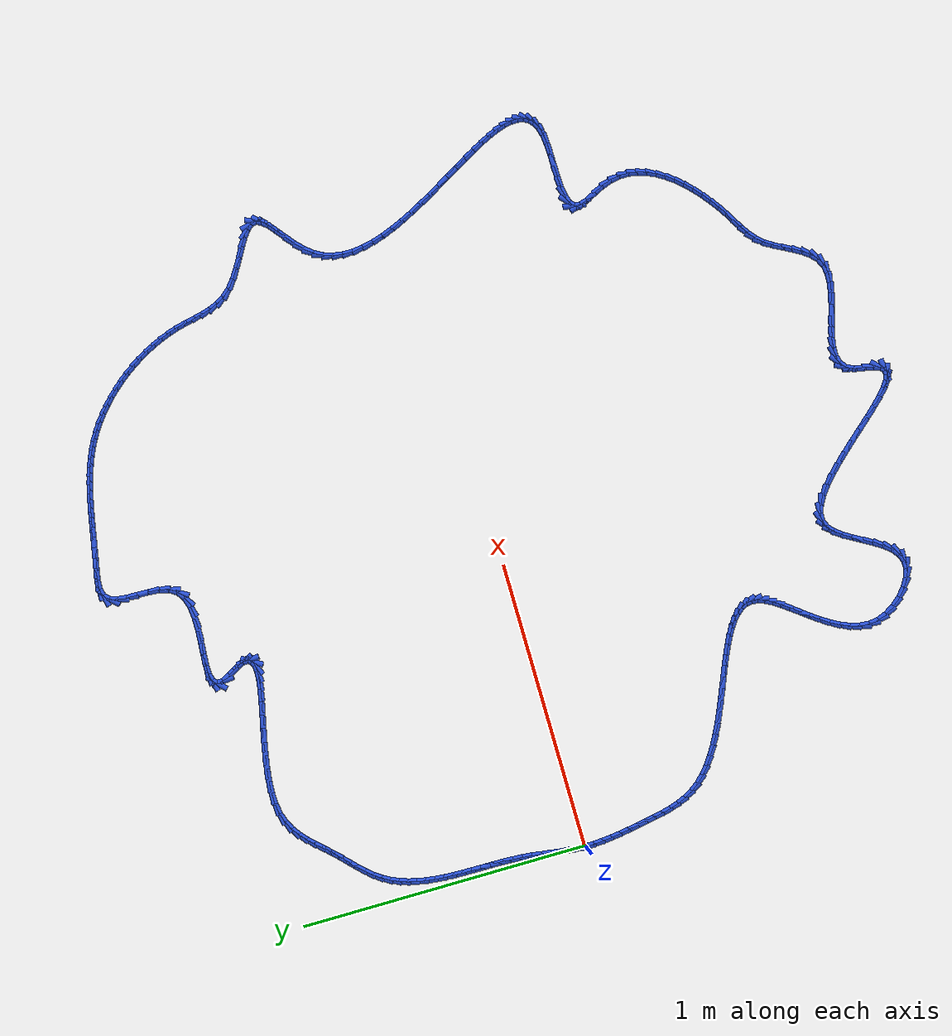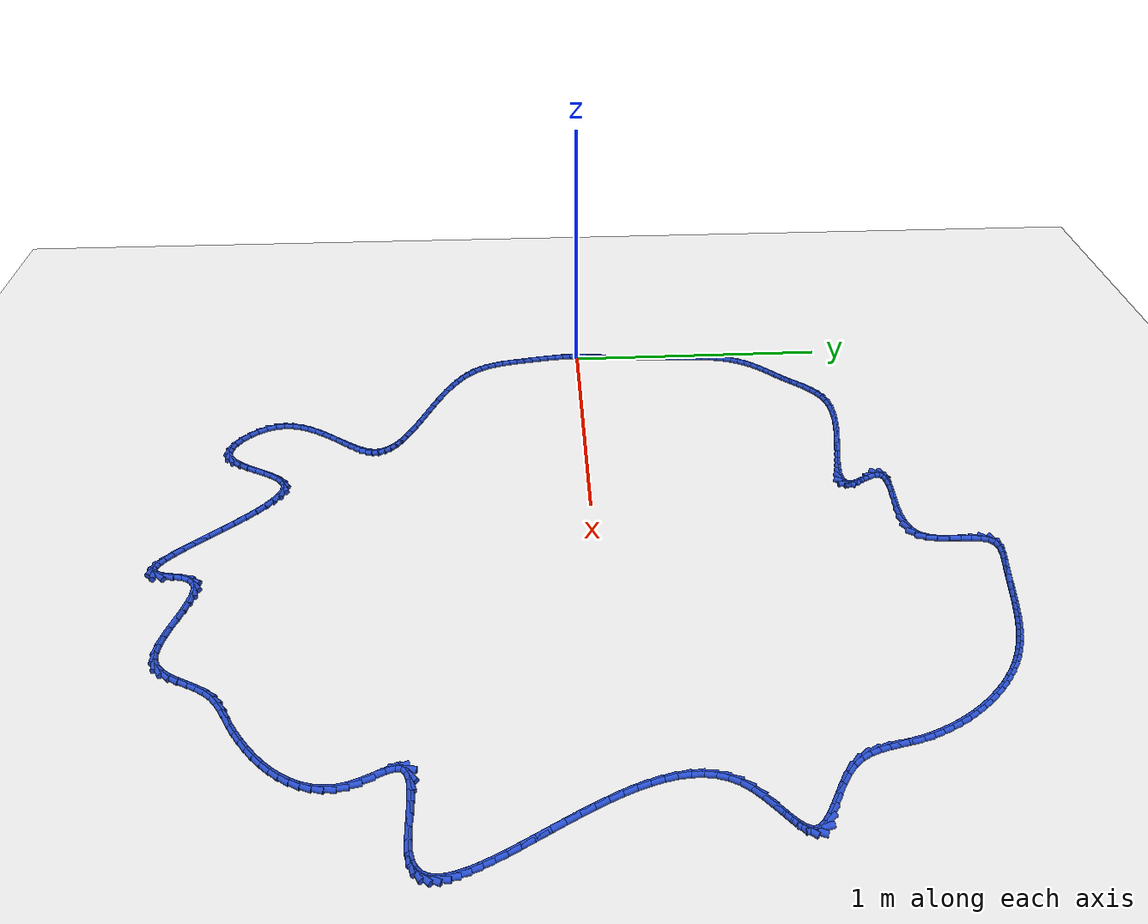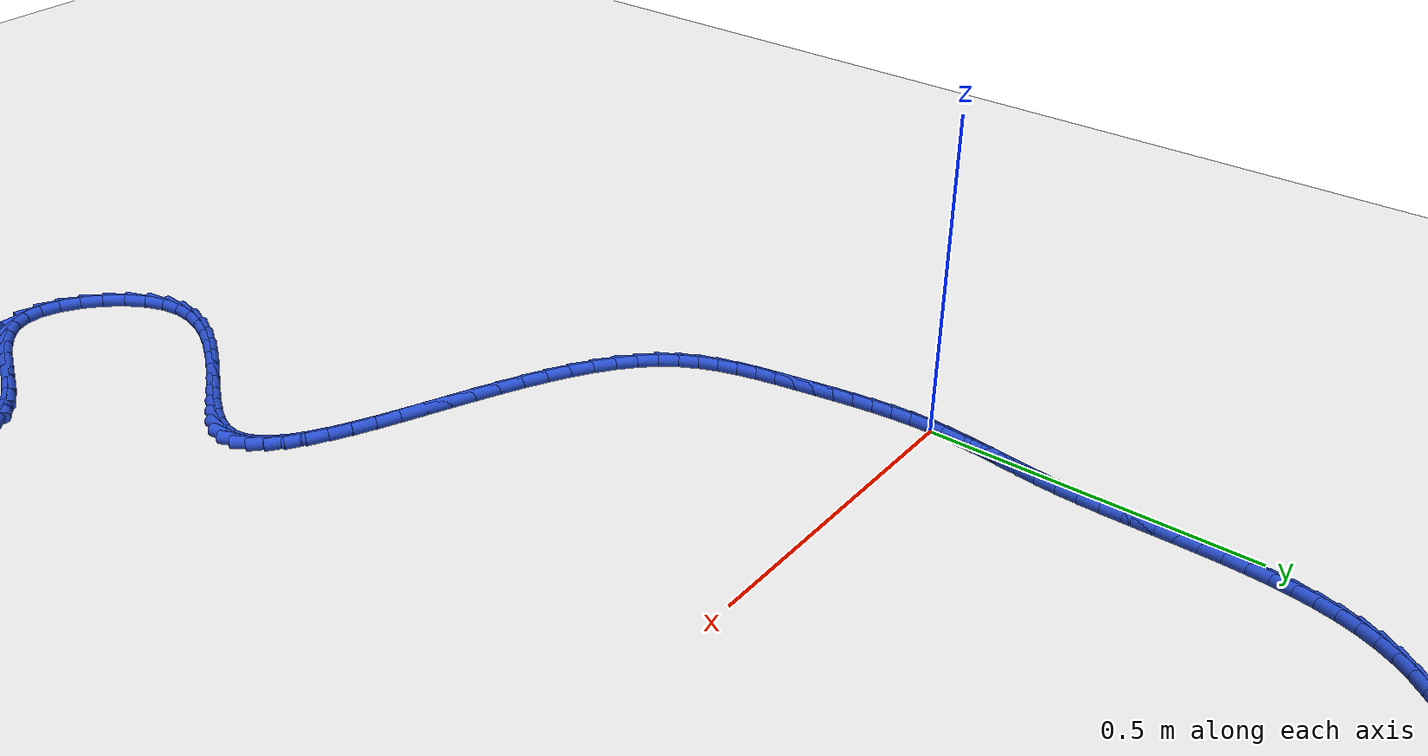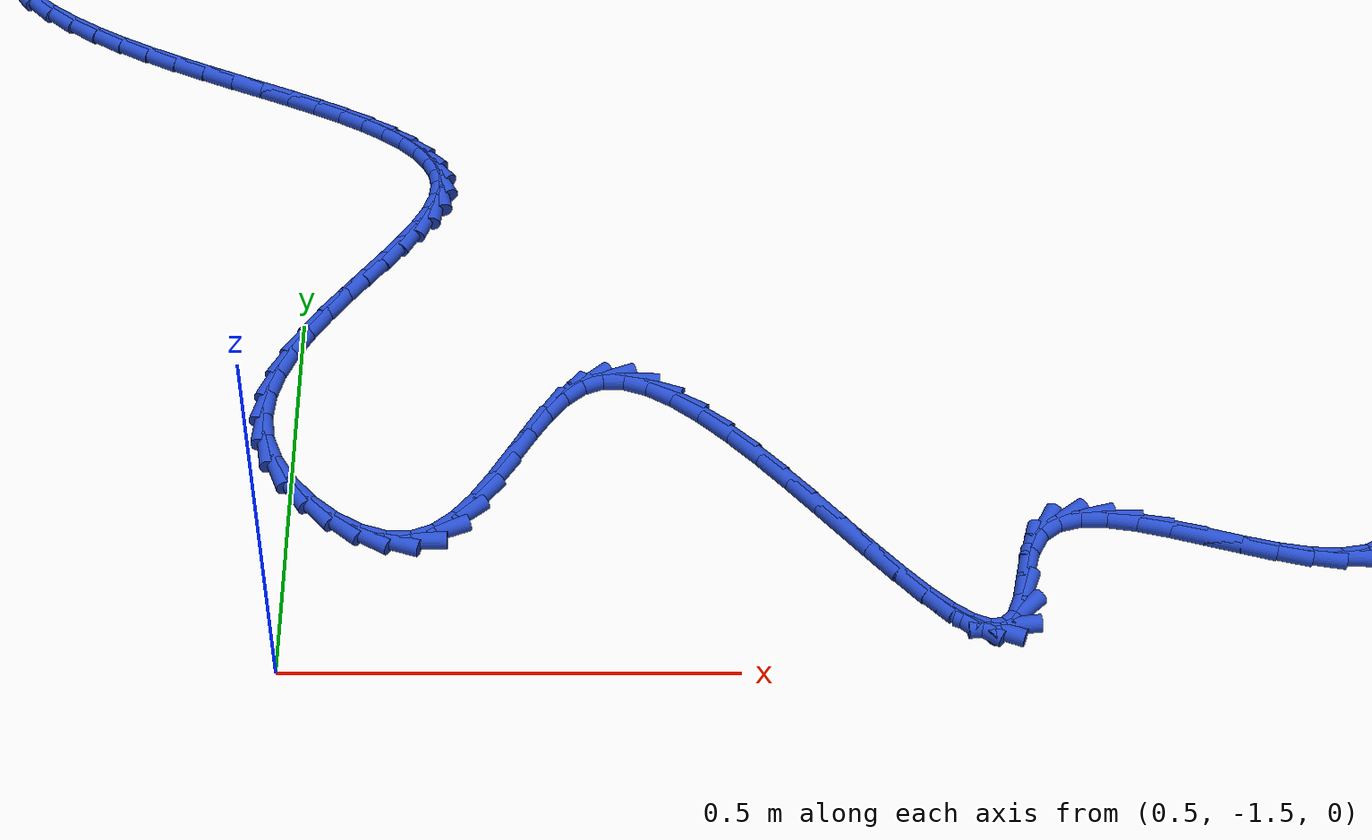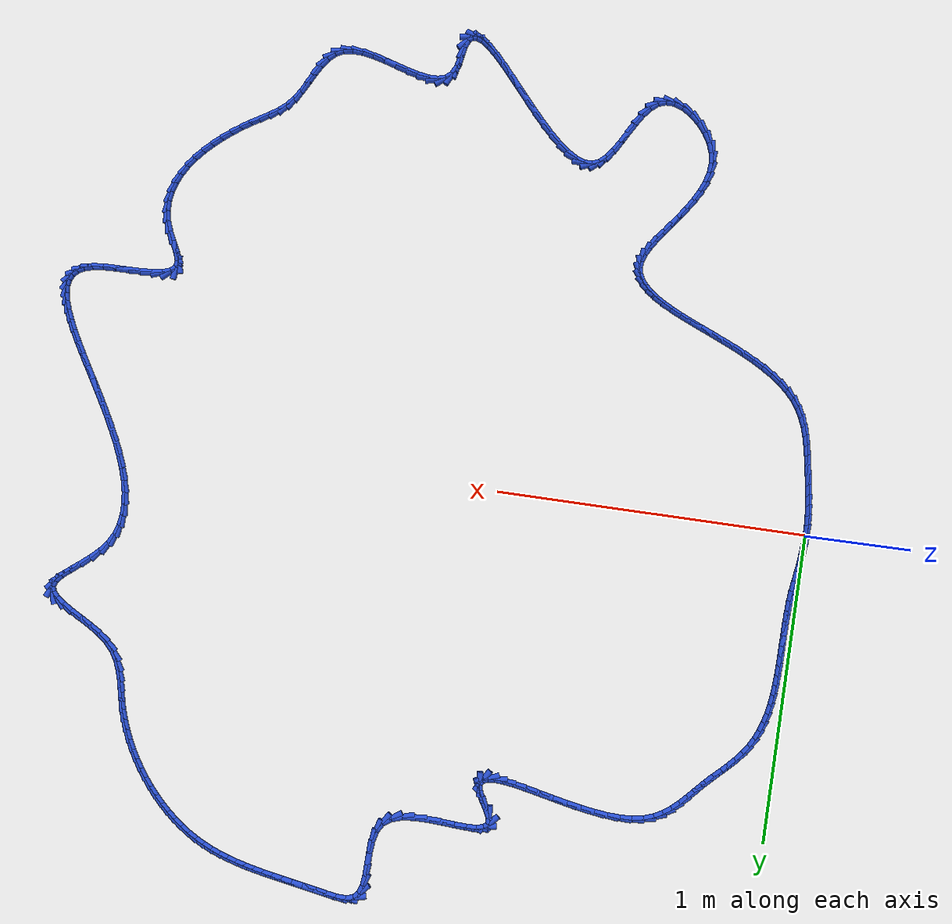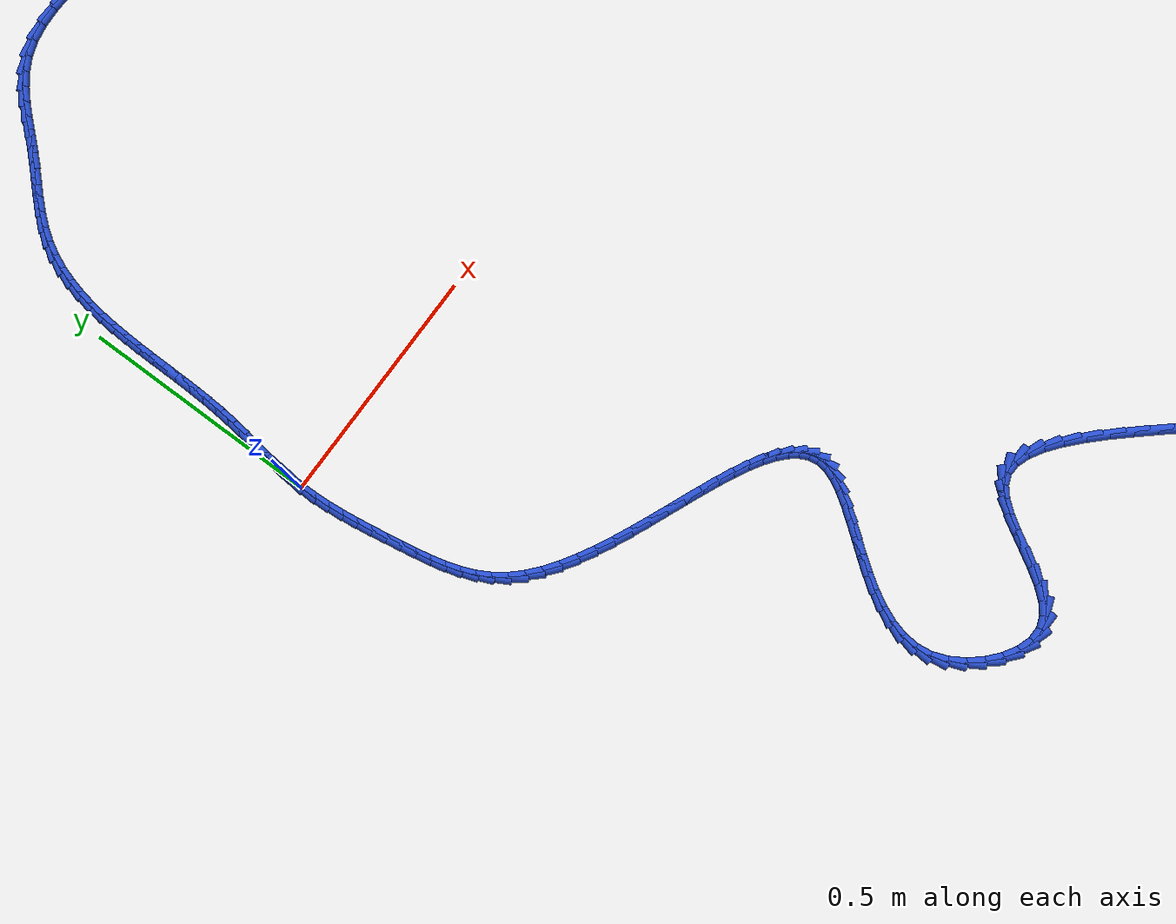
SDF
<sdf version="1.6">
 <world name="default">
  <light name="sun" type="directional">
   <pose>0 0 10 0 -0 0</pose>
   <diffuse>0.8 0.8 0.8 1</diffuse>
   <specular>0.2 0.2 0.2 1</specular>
   <attenuation>
    <range>1000</range>
    <constant>0.9</constant>
    <linear>0.01</linear>
    <quadratic>0.001</quadratic>
   </attenuation>
   <direction>-0.5 0.1 -0.9</direction>
  </light>
  <model name="ground_plane">
   <static>1</static>
   <link name="link">
    <collision name="collision">
     <geometry><plane><normal>0 0 1</normal><size>100 100</size></plane></geometry>
     <surface><friction><ode><mu>100</mu><mu2>50</mu2></ode></friction></surface>
    </collision>
    <visual name="visual">
     <cast_shadows>0</cast_shadows>
     <geometry><plane><normal>0 0 1</normal><size>100 100</size></plane></geometry>
     <material>
      <script><uri>file://media/materials/scripts/gazebo.material</uri><name>Gazebo/WhiteGlow</name></script>
     </material>
    </visual>
   </link>
  </model>
  <gravity>0 0 -9.8</gravity>
  <magnetic_field>6e-06 2.3e-05 -4.2e-05</magnetic_field>
  <atmosphere type="adiabatic"/>
  <physics name="default_physics" default="0" type="ode">
   <max_step_size>0.001</max_step_size>
   <real_time_factor>1</real_time_factor>
   <real_time_update_rate>1000</real_time_update_rate>
  </physics>
  <scene><ambient>0.4 0.4 0.4 1</ambient><background>0.7 0.7 0.7 1</background><shadows>1</shadows></scene>
  <spherical_coordinates>
   <surface_model>EARTH_WGS84</surface_model>
   <latitude_deg>0</latitude_deg>
   <longitude_deg>0</longitude_deg>
   <elevation>0</elevation>
   <heading_deg>0</heading_deg>
  </spherical_coordinates>
  <model name="line">
   <link name="link_0">
    <pose>6.071532165918825e-18 2.0816681711721685e-17 0.01 0 1.57 1.5228413119064752</pose>
    <collision name="collision">
     <geometry><cylinder><radius>0.01</radius><length>0.08</length></cylinder></geometry>
    </collision>
    <visual name="visual">
     <material>
      <script><name>Gazebo/Blue</name><uri>file://media/materials/scripts/gazebo.material</uri></script>
     </material>
     <geometry><cylinder><radius>0.01</radius><length>0.08</length></cylinder></geometry>
    </visual>
   </link>
   <link name="link_1">
    <pose>0.0014991091214428918 0.031236770333529493 0.01 0 1.57 1.479106439253478</pose>
    <collision name="collision">
     <geometry><cylinder><radius>0.01</radius><length>0.08</length></cylinder></geometry>
    </collision>
    <visual name="visual">
     <material>
      <script><name>Gazebo/Blue</name><uri>file://media/materials/scripts/gazebo.material</uri></script>
     </material>
     <geometry><cylinder><radius>0.01</radius><length>0.08</length></cylinder></geometry>
    </visual>
   </link>
   <link name="link_2">
    <pose>0.004370735368496305 0.06246785286678825 0.01 0 1.57 1.4498907104379026</pose>
    <collision name="collision">
     <geometry><cylinder><radius>0.01</radius><length>0.08</length></cylinder></geometry>
    </collision>
    <visual name="visual">
     <material>
      <script><name>Gazebo/Blue</name><uri>file://media/materials/scripts/gazebo.material</uri></script>
     </material>
     <geometry><cylinder><radius>0.01</radius><length>0.08</length></cylinder></geometry>
    </visual>
   </link>
   <link name="link_3">
    <pose>0.008175191530294404 0.09378070767584436 0.01 0 1.57 1.4351255741908735</pose>
    <collision name="collision">
     <geometry><cylinder><radius>0.01</radius><length>0.08</length></cylinder></geometry>
    </collision>
    <visual name="visual">
     <material>
      <script><name>Gazebo/Blue</name><uri>file://media/materials/scripts/gazebo.material</uri></script>
     </material>
     <geometry><cylinder><radius>0.01</radius><length>0.08</length></cylinder></geometry>
    </visual>
   </link>
   <link name="link_4">
    <pose>0.012472790395971331 0.12526279483676592 0.01 0 1.57 1.4345560407025166</pose>
    <collision name="collision">
     <geometry><cylinder><radius>0.01</radius><length>0.08</length></cylinder></geometry>
    </collision>
    <visual name="visual">
     <material>
      <script><name>Gazebo/Blue</name><uri>file://media/materials/scripts/gazebo.material</uri></script>
     </material>
     <geometry><cylinder><radius>0.01</radius><length>0.08</length></cylinder></geometry>
    </visual>
   </link>
   <link name="link_5">
    <pose>0.016823844754661234 0.15700157442562102 0.01 0 1.57 1.4478393030656875</pose>
    <collision name="collision">
     <geometry><cylinder><radius>0.01</radius><length>0.08</length></cylinder></geometry>
    </collision>
    <visual name="visual">
     <material>
      <script><name>Gazebo/Blue</name><uri>file://media/materials/scripts/gazebo.material</uri></script>
     </material>
     <geometry><cylinder><radius>0.01</radius><length>0.08</length></cylinder></geometry>
    </visual>
   </link>
   <link name="link_6">
    <pose>0.020788667395498277 0.18908450651847775 0.01 0 1.57 1.4745252321055384</pose>
    <collision name="collision">
     <geometry><cylinder><radius>0.01</radius><length>0.08</length></cylinder></geometry>
    </collision>
    <visual name="visual">
     <material>
      <script><name>Gazebo/Blue</name><uri>file://media/materials/scripts/gazebo.material</uri></script>
     </material>
     <geometry><cylinder><radius>0.01</radius><length>0.08</length></cylinder></geometry>
    </visual>
   </link>
   <link name="link_7">
    <pose>0.023928555919146176 0.2215987543637677 0.01 0 1.57 1.5078525602732806</pose>
    <collision name="collision">
     <geometry><cylinder><radius>0.01</radius><length>0.08</length></cylinder></geometry>
    </collision>
    <visual name="visual">
     <material>
      <script><name>Gazebo/Blue</name><uri>file://media/materials/scripts/gazebo.material</uri></script>
     </material>
     <geometry><cylinder><radius>0.01</radius><length>0.08</length></cylinder></geometry>
    </visual>
   </link>
   <link name="link_8">
    <pose>0.026006675584604254 0.2545706371822961 0.01 0 1.57 1.5340025860333557</pose>
    <collision name="collision">
     <geometry><cylinder><radius>0.01</radius><length>0.08</length></cylinder></geometry>
    </collision>
    <visual name="visual">
     <material>
      <script><name>Gazebo/Blue</name><uri>file://media/materials/scripts/gazebo.material</uri></script>
     </material>
     <geometry><cylinder><radius>0.01</radius><length>0.08</length></cylinder></geometry>
    </visual>
   </link>
   <link name="link_9">
    <pose>0.0272332368678649 0.2878917322963527 0.01 0 1.57 1.5515645675860368</pose>
    <collision name="collision">
     <geometry><cylinder><radius>0.01</radius><length>0.08</length></cylinder></geometry>
    </collision>
    <visual name="visual">
     <material>
      <script><name>Gazebo/Blue</name><uri>file://media/materials/scripts/gazebo.material</uri></script>
     </material>
     <geometry><cylinder><radius>0.01</radius><length>0.08</length></cylinder></geometry>
    </visual>
   </link>
   <link name="link_10">
    <pose>0.027878422863744184 0.32143554094953986 0.01 0 1.57 1.5608681877677697</pose>
    <collision name="collision">
     <geometry><cylinder><radius>0.01</radius><length>0.08</length></cylinder></geometry>
    </collision>
    <visual name="visual">
     <material>
      <script><name>Gazebo/Blue</name><uri>file://media/materials/scripts/gazebo.material</uri></script>
     </material>
     <geometry><cylinder><radius>0.01</radius><length>0.08</length></cylinder></geometry>
    </visual>
   </link>
   <link name="link_11">
    <pose>0.028212416667058145 0.35507556438546006 0.01 0 1.57 1.562079291517804</pose>
    <collision name="collision">
     <geometry><cylinder><radius>0.01</radius><length>0.08</length></cylinder></geometry>
    </collision>
    <visual name="visual">
     <material>
      <script><name>Gazebo/Blue</name><uri>file://media/materials/scripts/gazebo.material</uri></script>
     </material>
     <geometry><cylinder><radius>0.01</radius><length>0.08</length></cylinder></geometry>
    </visual>
   </link>
   <link name="link_12">
    <pose>0.02850540137262282 0.38868530384771566 0.01 0 1.57 1.555188848269538</pose>
    <collision name="collision">
     <geometry><cylinder><radius>0.01</radius><length>0.08</length></cylinder></geometry>
    </collision>
    <visual name="visual">
     <material>
      <script><name>Gazebo/Blue</name><uri>file://media/materials/scripts/gazebo.material</uri></script>
     </material>
     <geometry><cylinder><radius>0.01</radius><length>0.08</length></cylinder></geometry>
    </visual>
   </link>
   <link name="link_13">
    <pose>0.029027560075254276 0.42213826057990905 0.01 0 1.57 1.5400093798811614</pose>
    <collision name="collision">
     <geometry><cylinder><radius>0.01</radius><length>0.08</length></cylinder></geometry>
    </collision>
    <visual name="visual">
     <material>
      <script><name>Gazebo/Blue</name><uri>file://media/materials/scripts/gazebo.material</uri></script>
     </material>
     <geometry><cylinder><radius>0.01</radius><length>0.08</length></cylinder></geometry>
    </visual>
   </link>
   <link name="link_14">
    <pose>0.030049075869768536 0.45530793582564244 0.01 0 1.57 1.516178488262326</pose>
    <collision name="collision">
     <geometry><cylinder><radius>0.01</radius><length>0.08</length></cylinder></geometry>
    </collision>
    <visual name="visual">
     <material>
      <script><name>Gazebo/Blue</name><uri>file://media/materials/scripts/gazebo.material</uri></script>
     </material>
     <geometry><cylinder><radius>0.01</radius><length>0.08</length></cylinder></geometry>
    </visual>
   </link>
   <link name="link_15">
    <pose>0.03184013185098166 0.48806783082851846 0.01 0 1.57 1.4831732978650962</pose>
    <collision name="collision">
     <geometry><cylinder><radius>0.01</radius><length>0.08</length></cylinder></geometry>
    </collision>
    <visual name="visual">
     <material>
      <script><name>Gazebo/Blue</name><uri>file://media/materials/scripts/gazebo.material</uri></script>
     </material>
     <geometry><cylinder><radius>0.01</radius><length>0.08</length></cylinder></geometry>
    </visual>
   </link>
   <link name="link_16">
    <pose>0.03467091111370968 0.5202914468321391 0.01 0 1.57 1.4403444480942433</pose>
    <collision name="collision">
     <geometry><cylinder><radius>0.01</radius><length>0.08</length></cylinder></geometry>
    </collision>
    <visual name="visual">
     <material>
      <script><name>Gazebo/Blue</name><uri>file://media/materials/scripts/gazebo.material</uri></script>
     </material>
     <geometry><cylinder><radius>0.01</radius><length>0.08</length></cylinder></geometry>
    </visual>
   </link>
   <link name="link_17">
    <pose>0.03881159675276868 0.5518522850801075 0.01 0 1.57 1.386983747950167</pose>
    <collision name="collision">
     <geometry><cylinder><radius>0.01</radius><length>0.08</length></cylinder></geometry>
    </collision>
    <visual name="visual">
     <material>
      <script><name>Gazebo/Blue</name><uri>file://media/materials/scripts/gazebo.material</uri></script>
     </material>
     <geometry><cylinder><radius>0.01</radius><length>0.08</length></cylinder></geometry>
    </visual>
   </link>
   <link name="link_18">
    <pose>0.04453237186297462 0.5826238468160249 0.01 0 1.57 1.3224442605211304</pose>
    <collision name="collision">
     <geometry><cylinder><radius>0.01</radius><length>0.08</length></cylinder></geometry>
    </collision>
    <visual name="visual">
     <material>
      <script><name>Gazebo/Blue</name><uri>file://media/materials/scripts/gazebo.material</uri></script>
     </material>
     <geometry><cylinder><radius>0.01</radius><length>0.08</length></cylinder></geometry>
    </visual>
   </link>
   <link name="link_19">
    <pose>0.05210341953914363 0.6124796332834946 0.01 0 1.57 1.2463307886620099</pose>
    <collision name="collision">
     <geometry><cylinder><radius>0.01</radius><length>0.08</length></cylinder></geometry>
    </collision>
    <visual name="visual">
     <material>
      <script><name>Gazebo/Blue</name><uri>file://media/materials/scripts/gazebo.material</uri></script>
     </material>
     <geometry><cylinder><radius>0.01</radius><length>0.08</length></cylinder></geometry>
    </visual>
   </link>
   <link name="link_20">
    <pose>0.06179492287609177 0.6412931457261188 0.01 0 1.57 1.1587633906094261</pose>
    <collision name="collision">
     <geometry><cylinder><radius>0.01</radius><length>0.08</length></cylinder></geometry>
    </collision>
    <visual name="visual">
     <material>
      <script><name>Gazebo/Blue</name><uri>file://media/materials/scripts/gazebo.material</uri></script>
     </material>
     <geometry><cylinder><radius>0.01</radius><length>0.08</length></cylinder></geometry>
    </visual>
   </link>
   <link name="link_21">
    <pose>0.07387706496863501 0.6689378853874994 0.01 0 1.57 1.0606761023043398</pose>
    <collision name="collision">
     <geometry><cylinder><radius>0.01</radius><length>0.08</length></cylinder></geometry>
    </collision>
    <visual name="visual">
     <material>
      <script><name>Gazebo/Blue</name><uri>file://media/materials/scripts/gazebo.material</uri></script>
     </material>
     <geometry><cylinder><radius>0.01</radius><length>0.08</length></cylinder></geometry>
    </visual>
   </link>
   <link name="link_22">
    <pose>0.08862002891158942 0.6952873535112394 0.01 0 1.57 0.9564874920206814</pose>
    <collision name="collision">
     <geometry><cylinder><radius>0.01</radius><length>0.08</length></cylinder></geometry>
    </collision>
    <visual name="visual">
     <material>
      <script><name>Gazebo/Blue</name><uri>file://media/materials/scripts/gazebo.material</uri></script>
     </material>
     <geometry><cylinder><radius>0.01</radius><length>0.08</length></cylinder></geometry>
    </visual>
   </link>
   <link name="link_23">
    <pose>0.10622759375755328 0.7202501618423135 0.01 0 1.57 0.8697075107137532</pose>
    <collision name="collision">
     <geometry><cylinder><radius>0.01</radius><length>0.08</length></cylinder></geometry>
    </collision>
    <visual name="visual">
     <material>
      <script><name>Gazebo/Blue</name><uri>file://media/materials/scripts/gazebo.material</uri></script>
     </material>
     <geometry><cylinder><radius>0.01</radius><length>0.08</length></cylinder></geometry>
    </visual>
   </link>
   <link name="link_24">
    <pose>0.12631498115132753 0.7440461162184676 0.01 0 1.57 0.810716877164615</pose>
    <collision name="collision">
     <geometry><cylinder><radius>0.01</radius><length>0.08</length></cylinder></geometry>
    </collision>
    <visual name="visual">
     <material>
      <script><name>Gazebo/Blue</name><uri>file://media/materials/scripts/gazebo.material</uri></script>
     </material>
     <geometry><cylinder><radius>0.01</radius><length>0.08</length></cylinder></geometry>
    </visual>
   </link>
   <link name="link_25">
    <pose>0.14818981725444022 0.7670576606433932 0.01 0 1.57 0.7775824461752667</pose>
    <collision name="collision">
     <geometry><cylinder><radius>0.01</radius><length>0.08</length></cylinder></geometry>
    </collision>
    <visual name="visual">
     <material>
      <script><name>Gazebo/Blue</name><uri>file://media/materials/scripts/gazebo.material</uri></script>
     </material>
     <geometry><cylinder><radius>0.01</radius><length>0.08</length></cylinder></geometry>
    </visual>
   </link>
   <link name="link_26">
    <pose>0.17115704712089375 0.7896686567307086 0.01 0 1.57 0.7686399820368625</pose>
    <collision name="collision">
     <geometry><cylinder><radius>0.01</radius><length>0.08</length></cylinder></geometry>
    </collision>
    <visual name="visual">
     <material>
      <script><name>Gazebo/Blue</name><uri>file://media/materials/scripts/gazebo.material</uri></script>
     </material>
     <geometry><cylinder><radius>0.01</radius><length>0.08</length></cylinder></geometry>
    </visual>
   </link>
   <link name="link_27">
    <pose>0.19452161580469068 0.8122629660940324 0.01 0 1.57 0.783108962321759</pose>
    <collision name="collision">
     <geometry><cylinder><radius>0.01</radius><length>0.08</length></cylinder></geometry>
    </collision>
    <visual name="visual">
     <material>
      <script><name>Gazebo/Blue</name><uri>file://media/materials/scripts/gazebo.material</uri></script>
     </material>
     <geometry><cylinder><radius>0.01</radius><length>0.08</length></cylinder></geometry>
    </visual>
   </link>
   <link name="link_28">
    <pose>0.2175884683598337 0.8352244503469832 0.01 0 1.57 0.8145725686481282</pose>
    <collision name="collision">
     <geometry><cylinder><radius>0.01</radius><length>0.08</length></cylinder></geometry>
    </collision>
    <visual name="visual">
     <material>
      <script><name>Gazebo/Blue</name><uri>file://media/materials/scripts/gazebo.material</uri></script>
     </material>
     <geometry><cylinder><radius>0.01</radius><length>0.08</length></cylinder></geometry>
    </visual>
   </link>
   <link name="link_29">
    <pose>0.23982771956075666 0.8588007215189424 0.01 0 1.57 0.8241641632022959</pose>
    <collision name="collision">
     <geometry><cylinder><radius>0.01</radius><length>0.08</length></cylinder></geometry>
    </collision>
    <visual name="visual">
     <material>
      <script><name>Gazebo/Blue</name><uri>file://media/materials/scripts/gazebo.material</uri></script>
     </material>
     <geometry><cylinder><radius>0.01</radius><length>0.08</length></cylinder></geometry>
    </visual>
   </link>
   <link name="link_30">
    <pose>0.2616917057526232 0.8824291506320963 0.01 0 1.57 0.796854420594403</pose>
    <collision name="collision">
     <geometry><cylinder><radius>0.01</radius><length>0.08</length></cylinder></geometry>
    </collision>
    <visual name="visual">
     <material>
      <script><name>Gazebo/Blue</name><uri>file://media/materials/scripts/gazebo.material</uri></script>
     </material>
     <geometry><cylinder><radius>0.01</radius><length>0.08</length></cylinder></geometry>
    </visual>
   </link>
   <link name="link_31">
    <pose>0.28399439541838345 0.9052487959894997 0.01 0 1.57 0.7316204973585401</pose>
    <collision name="collision">
     <geometry><cylinder><radius>0.01</radius><length>0.08</length></cylinder></geometry>
    </collision>
    <visual name="visual">
     <material>
      <script><name>Gazebo/Blue</name><uri>file://media/materials/scripts/gazebo.material</uri></script>
     </material>
     <geometry><cylinder><radius>0.01</radius><length>0.08</length></cylinder></geometry>
    </visual>
   </link>
   <link name="link_32">
    <pose>0.3075503212400427 0.926398250482711 0.01 0 1.57 0.6283479717193791</pose>
    <collision name="collision">
     <geometry><cylinder><radius>0.01</radius><length>0.08</length></cylinder></geometry>
    </collision>
    <visual name="visual">
     <material>
      <script><name>Gazebo/Blue</name><uri>file://media/materials/scripts/gazebo.material</uri></script>
     </material>
     <geometry><cylinder><radius>0.01</radius><length>0.08</length></cylinder></geometry>
    </visual>
   </link>
   <link name="link_33">
    <pose>0.3331740158996063 0.945016107003289 0.01 0 1.57 0.49054853260155695</pose>
    <collision name="collision">
     <geometry><cylinder><radius>0.01</radius><length>0.08</length></cylinder></geometry>
    </collision>
    <visual name="visual">
     <material>
      <script><name>Gazebo/Blue</name><uri>file://media/materials/scripts/gazebo.material</uri></script>
     </material>
     <geometry><cylinder><radius>0.01</radius><length>0.08</length></cylinder></geometry>
    </visual>
   </link>
   <link name="link_34">
    <pose>0.3616800120790796 0.9602409584427918 0.01 0 1.57 0.32833620386717977</pose>
    <collision name="collision">
     <geometry><cylinder><radius>0.01</radius><length>0.08</length></cylinder></geometry>
    </collision>
    <visual name="visual">
     <material>
      <script><name>Gazebo/Blue</name><uri>file://media/materials/scripts/gazebo.material</uri></script>
     </material>
     <geometry><cylinder><radius>0.01</radius><length>0.08</length></cylinder></geometry>
    </visual>
   </link>
   <link name="link_35">
    <pose>0.393882842460468 0.9712113976927781 0.01 0 1.57 0.16401270620343095</pose>
    <collision name="collision">
     <geometry><cylinder><radius>0.01</radius><length>0.08</length></cylinder></geometry>
    </collision>
    <visual name="visual">
     <material>
      <script><name>Gazebo/Blue</name><uri>file://media/materials/scripts/gazebo.material</uri></script>
     </material>
     <geometry><cylinder><radius>0.01</radius><length>0.08</length></cylinder></geometry>
    </visual>
   </link>
   <link name="link_36">
    <pose>0.4303977751358432 0.9772545957248768 0.01 0 1.57 0.03739849756958112</pose>
    <collision name="collision">
     <geometry><cylinder><radius>0.01</radius><length>0.08</length></cylinder></geometry>
    </collision>
    <visual name="visual">
     <material>
      <script><name>Gazebo/Blue</name><uri>file://media/materials/scripts/gazebo.material</uri></script>
     </material>
     <geometry><cylinder><radius>0.01</radius><length>0.08</length></cylinder></geometry>
    </visual>
   </link>
   <link name="link_37">
    <pose>0.470714350804725 0.9787630784262082 0.01 0 1.57 -0.05225091464127412</pose>
    <collision name="collision">
     <geometry><cylinder><radius>0.01</radius><length>0.08</length></cylinder></geometry>
    </collision>
    <visual name="visual">
     <material>
      <script><name>Gazebo/Blue</name><uri>file://media/materials/scripts/gazebo.material</uri></script>
     </material>
     <geometry><cylinder><radius>0.01</radius><length>0.08</length></cylinder></geometry>
    </visual>
   </link>
   <link name="link_38">
    <pose>0.5139271915559751 0.9765031109087444 0.01 0 1.57 -0.11588036690892356</pose>
    <collision name="collision">
     <geometry><cylinder><radius>0.01</radius><length>0.08</length></cylinder></geometry>
    </collision>
    <visual name="visual">
     <material>
      <script><name>Gazebo/Blue</name><uri>file://media/materials/scripts/gazebo.material</uri></script>
     </material>
     <geometry><cylinder><radius>0.01</radius><length>0.08</length></cylinder></geometry>
    </visual>
   </link>
   <link name="link_39">
    <pose>0.5591304921454062 0.9712413626997422 0.01 0 1.57 -0.16056706052890735</pose>
    <collision name="collision">
     <geometry><cylinder><radius>0.01</radius><length>0.08</length></cylinder></geometry>
    </collision>
    <visual name="visual">
     <material>
      <script><name>Gazebo/Blue</name><uri>file://media/materials/scripts/gazebo.material</uri></script>
     </material>
     <geometry><cylinder><radius>0.01</radius><length>0.08</length></cylinder></geometry>
    </visual>
   </link>
   <link name="link_40">
    <pose>0.6054184473288297 0.9637445033264574 0.01 0 1.57 -0.1905978855281085</pose>
    <collision name="collision">
     <geometry><cylinder><radius>0.01</radius><length>0.08</length></cylinder></geometry>
    </collision>
    <visual name="visual">
     <material>
      <script><name>Gazebo/Blue</name><uri>file://media/materials/scripts/gazebo.material</uri></script>
     </material>
     <geometry><cylinder><radius>0.01</radius><length>0.08</length></cylinder></geometry>
    </visual>
   </link>
   <link name="link_41">
    <pose>0.651885251862058 0.954779202316149 0.01 0 1.57 -0.20828390359519258</pose>
    <collision name="collision">
     <geometry><cylinder><radius>0.01</radius><length>0.08</length></cylinder></geometry>
    </collision>
    <visual name="visual">
     <material>
      <script><name>Gazebo/Blue</name><uri>file://media/materials/scripts/gazebo.material</uri></script>
     </material>
     <geometry><cylinder><radius>0.01</radius><length>0.08</length></cylinder></geometry>
    </visual>
   </link>
   <link name="link_42">
    <pose>0.6976251005009027 0.9451121291960721 0.01 0 1.57 -0.21435678839201483</pose>
    <collision name="collision">
     <geometry><cylinder><radius>0.01</radius><length>0.08</length></cylinder></geometry>
    </collision>
    <visual name="visual">
     <material>
      <script><name>Gazebo/Blue</name><uri>file://media/materials/scripts/gazebo.material</uri></script>
     </material>
     <geometry><cylinder><radius>0.01</radius><length>0.08</length></cylinder></geometry>
    </visual>
   </link>
   <link name="link_43">
    <pose>0.7417321880011751 0.9355099534934844 0.01 0 1.57 -0.2079417215046066</pose>
    <collision name="collision">
     <geometry><cylinder><radius>0.01</radius><length>0.08</length></cylinder></geometry>
    </collision>
    <visual name="visual">
     <material>
      <script><name>Gazebo/Blue</name><uri>file://media/materials/scripts/gazebo.material</uri></script>
     </material>
     <geometry><cylinder><radius>0.01</radius><length>0.08</length></cylinder></geometry>
    </visual>
   </link>
   <link name="link_44">
    <pose>0.7833007091186882 0.9267393447356425 0.01 0 1.57 -0.18595841066379873</pose>
    <collision name="collision">
     <geometry><cylinder><radius>0.01</radius><length>0.08</length></cylinder></geometry>
    </collision>
    <visual name="visual">
     <material>
      <script><name>Gazebo/Blue</name><uri>file://media/materials/scripts/gazebo.material</uri></script>
     </material>
     <geometry><cylinder><radius>0.01</radius><length>0.08</length></cylinder></geometry>
    </visual>
   </link>
   <link name="link_45">
    <pose>0.8214248586092534 0.9195669724498038 0.01 0 1.57 -0.14139251127535413</pose>
    <collision name="collision">
     <geometry><cylinder><radius>0.01</radius><length>0.08</length></cylinder></geometry>
    </collision>
    <visual name="visual">
     <material>
      <script><name>Gazebo/Blue</name><uri>file://media/materials/scripts/gazebo.material</uri></script>
     </material>
     <geometry><cylinder><radius>0.01</radius><length>0.08</length></cylinder></geometry>
    </visual>
   </link>
   <link name="link_46">
    <pose>0.8551988312286829 0.9147595061632251 0.01 0 1.57 -0.05869857990196866</pose>
    <collision name="collision">
     <geometry><cylinder><radius>0.01</radius><length>0.08</length></cylinder></geometry>
    </collision>
    <visual name="visual">
     <material>
      <script><name>Gazebo/Blue</name><uri>file://media/materials/scripts/gazebo.material</uri></script>
     </material>
     <geometry><cylinder><radius>0.01</radius><length>0.08</length></cylinder></geometry>
    </visual>
   </link>
   <link name="link_47">
    <pose>0.8837168217327889 0.9130836154031634 0.01 0 1.57 0.0990810999384162</pose>
    <collision name="collision">
     <geometry><cylinder><radius>0.01</radius><length>0.08</length></cylinder></geometry>
    </collision>
    <visual name="visual">
     <material>
      <script><name>Gazebo/Blue</name><uri>file://media/materials/scripts/gazebo.material</uri></script>
     </material>
     <geometry><cylinder><radius>0.01</radius><length>0.08</length></cylinder></geometry>
    </visual>
   </link>
   <link name="link_48">
    <pose>0.9060730248773824 0.915305969696875 0.01 0 1.57 0.4232560459164627</pose>
    <collision name="collision">
     <geometry><cylinder><radius>0.01</radius><length>0.08</length></cylinder></geometry>
    </collision>
    <visual name="visual">
     <material>
      <script><name>Gazebo/Blue</name><uri>file://media/materials/scripts/gazebo.material</uri></script>
     </material>
     <geometry><cylinder><radius>0.01</radius><length>0.08</length></cylinder></geometry>
    </visual>
   </link>
   <link name="link_49">
    <pose>0.9213616354182765 0.9221932385716181 0.01 0 1.57 1.034931450594322</pose>
    <collision name="collision">
     <geometry><cylinder><radius>0.01</radius><length>0.08</length></cylinder></geometry>
    </collision>
    <visual name="visual">
     <material>
      <script><name>Gazebo/Blue</name><uri>file://media/materials/scripts/gazebo.material</uri></script>
     </material>
     <geometry><cylinder><radius>0.01</radius><length>0.08</length></cylinder></geometry>
    </visual>
   </link>
   <link name="link_50">
    <pose>0.9286768481112821 0.9345120915546483 0.01 0 1.57 -1.4865343956009753</pose>
    <collision name="collision">
     <geometry><cylinder><radius>0.01</radius><length>0.08</length></cylinder></geometry>
    </collision>
    <visual name="visual">
     <material>
      <script><name>Gazebo/Blue</name><uri>file://media/materials/scripts/gazebo.material</uri></script>
     </material>
     <geometry><cylinder><radius>0.01</radius><length>0.08</length></cylinder></geometry>
    </visual>
   </link>
   <link name="link_51">
    <pose>0.927112857712212 0.9530291981732235 0.01 0 1.57 -1.1547413814609242</pose>
    <collision name="collision">
     <geometry><cylinder><radius>0.01</radius><length>0.08</length></cylinder></geometry>
    </collision>
    <visual name="visual">
     <material>
      <script><name>Gazebo/Blue</name><uri>file://media/materials/scripts/gazebo.material</uri></script>
     </material>
     <geometry><cylinder><radius>0.01</radius><length>0.08</length></cylinder></geometry>
    </visual>
   </link>
   <link name="link_52">
    <pose>0.9158919618264509 0.9784245140293565 0.01 0 1.57 -1.0504726478481072</pose>
    <collision name="collision">
     <geometry><cylinder><radius>0.01</radius><length>0.08</length></cylinder></geometry>
    </collision>
    <visual name="visual">
     <material>
      <script><name>Gazebo/Blue</name><uri>file://media/materials/scripts/gazebo.material</uri></script>
     </material>
     <geometry><cylinder><radius>0.01</radius><length>0.08</length></cylinder></geometry>
    </visual>
   </link>
   <link name="link_53">
    <pose>0.8987671970805831 1.0083110983516304 0.01 0 1.57 -1.1200001222560645</pose>
    <collision name="collision">
     <geometry><cylinder><radius>0.01</radius><length>0.08</length></cylinder></geometry>
    </collision>
    <visual name="visual">
     <material>
      <script><name>Gazebo/Blue</name><uri>file://media/materials/scripts/gazebo.material</uri></script>
     </material>
     <geometry><cylinder><radius>0.01</radius><length>0.08</length></cylinder></geometry>
    </visual>
   </link>
   <link name="link_54">
    <pose>0.8851297245689341 1.0364855152224364 0.01 0 1.57 -1.5068946399165088</pose>
    <collision name="collision">
     <geometry><cylinder><radius>0.01</radius><length>0.08</length></cylinder></geometry>
    </collision>
    <visual name="visual">
     <material>
      <script><name>Gazebo/Blue</name><uri>file://media/materials/scripts/gazebo.material</uri></script>
     </material>
     <geometry><cylinder><radius>0.01</radius><length>0.08</length></cylinder></geometry>
    </visual>
   </link>
   <link name="link_55">
    <pose>0.8838091367168668 1.0571233093020576 0.01 0 1.57 0.788141834081551</pose>
    <collision name="collision">
     <geometry><cylinder><radius>0.01</radius><length>0.08</length></cylinder></geometry>
    </collision>
    <visual name="visual">
     <material>
      <script><name>Gazebo/Blue</name><uri>file://media/materials/scripts/gazebo.material</uri></script>
     </material>
     <geometry><cylinder><radius>0.01</radius><length>0.08</length></cylinder></geometry>
    </visual>
   </link>
   <link name="link_56">
    <pose>0.8961055142858649 1.0694873470995305 0.01 0 1.57 0.2440385374236169</pose>
    <collision name="collision">
     <geometry><cylinder><radius>0.01</radius><length>0.08</length></cylinder></geometry>
    </collision>
    <visual name="visual">
     <material>
      <script><name>Gazebo/Blue</name><uri>file://media/materials/scripts/gazebo.material</uri></script>
     </material>
     <geometry><cylinder><radius>0.01</radius><length>0.08</length></cylinder></geometry>
    </visual>
   </link>
   <link name="link_57">
    <pose>0.9196169722506263 1.0753417318934446 0.01 0 1.57 0.03485476970271121</pose>
    <collision name="collision">
     <geometry><cylinder><radius>0.01</radius><length>0.08</length></cylinder></geometry>
    </collision>
    <visual name="visual">
     <material>
      <script><name>Gazebo/Blue</name><uri>file://media/materials/scripts/gazebo.material</uri></script>
     </material>
     <geometry><cylinder><radius>0.01</radius><length>0.08</length></cylinder></geometry>
    </visual>
   </link>
   <link name="link_58">
    <pose>0.9519158842268163 1.0764679591365525 0.01 0 1.57 -0.047055105347707855</pose>
    <collision name="collision">
     <geometry><cylinder><radius>0.01</radius><length>0.08</length></cylinder></geometry>
    </collision>
    <visual name="visual">
     <material>
      <script><name>Gazebo/Blue</name><uri>file://media/materials/scripts/gazebo.material</uri></script>
     </material>
     <geometry><cylinder><radius>0.01</radius><length>0.08</length></cylinder></geometry>
    </visual>
   </link>
   <link name="link_59">
    <pose>0.990574623830099 1.0746475242816054 0.01 0 1.57 -0.06998496536472172</pose>
    <collision name="collision">
     <geometry><cylinder><radius>0.01</radius><length>0.08</length></cylinder></geometry>
    </collision>
    <visual name="visual">
     <material>
      <script><name>Gazebo/Blue</name><uri>file://media/materials/scripts/gazebo.material</uri></script>
     </material>
     <geometry><cylinder><radius>0.01</radius><length>0.08</length></cylinder></geometry>
    </visual>
   </link>
   <link name="link_60">
    <pose>1.0331655646761408 1.0716619227813566 0.01 0 1.57 -0.05367885135740392</pose>
    <collision name="collision">
     <geometry><cylinder><radius>0.01</radius><length>0.08</length></cylinder></geometry>
    </collision>
    <visual name="visual">
     <material>
      <script><name>Gazebo/Blue</name><uri>file://media/materials/scripts/gazebo.material</uri></script>
     </material>
     <geometry><cylinder><radius>0.01</radius><length>0.08</length></cylinder></geometry>
    </visual>
   </link>
   <link name="link_61">
    <pose>1.077261080380606 1.0692926500885571 0.01 0 1.57 0.0006613373543472396</pose>
    <collision name="collision">
     <geometry><cylinder><radius>0.01</radius><length>0.08</length></cylinder></geometry>
    </collision>
    <visual name="visual">
     <material>
      <script><name>Gazebo/Blue</name><uri>file://media/materials/scripts/gazebo.material</uri></script>
     </material>
     <geometry><cylinder><radius>0.01</radius><length>0.08</length></cylinder></geometry>
    </visual>
   </link>
   <link name="link_62">
    <pose>1.1204335445591598 1.0693212016559601 0.01 0 1.57 0.10527689938691903</pose>
    <collision name="collision">
     <geometry><cylinder><radius>0.01</radius><length>0.08</length></cylinder></geometry>
    </collision>
    <visual name="visual">
     <material>
      <script><name>Gazebo/Blue</name><uri>file://media/materials/scripts/gazebo.material</uri></script>
     </material>
     <geometry><cylinder><radius>0.01</radius><length>0.08</length></cylinder></geometry>
    </visual>
   </link>
   <link name="link_63">
    <pose>1.1602553308274681 1.0735290729363176 0.01 0 1.57 0.290260967126054</pose>
    <collision name="collision">
     <geometry><cylinder><radius>0.01</radius><length>0.08</length></cylinder></geometry>
    </collision>
    <visual name="visual">
     <material>
      <script><name>Gazebo/Blue</name><uri>file://media/materials/scripts/gazebo.material</uri></script>
     </material>
     <geometry><cylinder><radius>0.01</radius><length>0.08</length></cylinder></geometry>
    </visual>
   </link>
   <link name="link_64">
    <pose>1.1942988128011955 1.0836977593823813 0.01 0 1.57 0.6061295584787272</pose>
    <collision name="collision">
     <geometry><cylinder><radius>0.01</radius><length>0.08</length></cylinder></geometry>
    </collision>
    <visual name="visual">
     <material>
      <script><name>Gazebo/Blue</name><uri>file://media/materials/scripts/gazebo.material</uri></script>
     </material>
     <geometry><cylinder><radius>0.01</radius><length>0.08</length></cylinder></geometry>
    </visual>
   </link>
   <link name="link_65">
    <pose>1.2201370600332901 1.1016081417591619 0.01 0 1.57 1.0193299710873618</pose>
    <collision name="collision">
     <geometry><cylinder><radius>0.01</radius><length>0.08</length></cylinder></geometry>
    </collision>
    <visual name="visual">
     <material>
      <script><name>Gazebo/Blue</name><uri>file://media/materials/scripts/gazebo.material</uri></script>
     </material>
     <geometry><cylinder><radius>0.01</radius><length>0.08</length></cylinder></geometry>
    </visual>
   </link>
   <link name="link_66">
    <pose>1.236424328470539 1.128086141184387 0.01 0 1.57 1.31417227078528</pose>
    <collision name="collision">
     <geometry><cylinder><radius>0.01</radius><length>0.08</length></cylinder></geometry>
    </collision>
    <visual name="visual">
     <material>
      <script><name>Gazebo/Blue</name><uri>file://media/materials/scripts/gazebo.material</uri></script>
     </material>
     <geometry><cylinder><radius>0.01</radius><length>0.08</length></cylinder></geometry>
    </visual>
   </link>
   <link name="link_67">
    <pose>1.2450804907800683 1.1610733174767547 0.01 0 1.57 1.4746304507638437</pose>
    <collision name="collision">
     <geometry><cylinder><radius>0.01</radius><length>0.08</length></cylinder></geometry>
    </collision>
    <visual name="visual">
     <material>
      <script><name>Gazebo/Blue</name><uri>file://media/materials/scripts/gazebo.material</uri></script>
     </material>
     <geometry><cylinder><radius>0.01</radius><length>0.08</length></cylinder></geometry>
    </visual>
   </link>
   <link name="link_68">
    <pose>1.2486395546948186 1.197968794655572 0.01 0 1.57 1.5447316132832647</pose>
    <collision name="collision">
     <geometry><cylinder><radius>0.01</radius><length>0.08</length></cylinder></geometry>
    </collision>
    <visual name="visual">
     <material>
      <script><name>Gazebo/Blue</name><uri>file://media/materials/scripts/gazebo.material</uri></script>
     </material>
     <geometry><cylinder><radius>0.01</radius><length>0.08</length></cylinder></geometry>
    </visual>
   </link>
   <link name="link_69">
    <pose>1.2496355279477291 1.236171696740145 0.01 0 1.57 1.5446060363947451</pose>
    <collision name="collision">
     <geometry><cylinder><radius>0.01</radius><length>0.08</length></cylinder></geometry>
    </collision>
    <visual name="visual">
     <material>
      <script><name>Gazebo/Blue</name><uri>file://media/materials/scripts/gazebo.material</uri></script>
     </material>
     <geometry><cylinder><radius>0.01</radius><length>0.08</length></cylinder></geometry>
    </visual>
   </link>
   <link name="link_70">
    <pose>1.250602418271741 1.2730811477497812 0.01 0 1.57 1.4660230734352857</pose>
    <collision name="collision">
     <geometry><cylinder><radius>0.01</radius><length>0.08</length></cylinder></geometry>
    </collision>
    <visual name="visual">
     <material>
      <script><name>Gazebo/Blue</name><uri>file://media/materials/scripts/gazebo.material</uri></script>
     </material>
     <geometry><cylinder><radius>0.01</radius><length>0.08</length></cylinder></geometry>
    </visual>
   </link>
   <link name="link_71">
    <pose>1.2540742333997934 1.3060962717037867 0.01 0 1.57 1.2602599292706624</pose>
    <collision name="collision">
     <geometry><cylinder><radius>0.01</radius><length>0.08</length></cylinder></geometry>
    </collision>
    <visual name="visual">
     <material>
      <script><name>Gazebo/Blue</name><uri>file://media/materials/scripts/gazebo.material</uri></script>
     </material>
     <geometry><cylinder><radius>0.01</radius><length>0.08</length></cylinder></geometry>
    </visual>
   </link>
   <link name="link_72">
    <pose>1.2625849810648262 1.332616192621468 0.01 0 1.57 0.8253724636693989</pose>
    <collision name="collision">
     <geometry><cylinder><radius>0.01</radius><length>0.08</length></cylinder></geometry>
    </collision>
    <visual name="visual">
     <material>
      <script><name>Gazebo/Blue</name><uri>file://media/materials/scripts/gazebo.material</uri></script>
     </material>
     <geometry><cylinder><radius>0.01</radius><length>0.08</length></cylinder></geometry>
    </visual>
   </link>
   <link name="link_73">
    <pose>1.2786686689997797 1.3500400345221317 0.01 0 1.57 0.26004808370753746</pose>
    <collision name="collision">
     <geometry><cylinder><radius>0.01</radius><length>0.08</length></cylinder></geometry>
    </collision>
    <visual name="visual">
     <material>
      <script><name>Gazebo/Blue</name><uri>file://media/materials/scripts/gazebo.material</uri></script>
     </material>
     <geometry><cylinder><radius>0.01</radius><length>0.08</length></cylinder></geometry>
    </visual>
   </link>
   <link name="link_74">
    <pose>1.3039321545466427 1.3567619666410027 0.01 0 1.57 -0.044521353887577164</pose>
    <collision name="collision">
     <geometry><cylinder><radius>0.01</radius><length>0.08</length></cylinder></geometry>
    </collision>
    <visual name="visual">
     <material>
      <script><name>Gazebo/Blue</name><uri>file://media/materials/scripts/gazebo.material</uri></script>
     </material>
     <geometry><cylinder><radius>0.01</radius><length>0.08</length></cylinder></geometry>
    </visual>
   </link>
   <link name="link_75">
    <pose>1.3361135012512961 1.355328262117658 0.01 0 1.57 -0.16484548316431186</pose>
    <collision name="collision">
     <geometry><cylinder><radius>0.01</radius><length>0.08</length></cylinder></geometry>
    </collision>
    <visual name="visual">
     <material>
      <script><name>Gazebo/Blue</name><uri>file://media/materials/scripts/gazebo.material</uri></script>
     </material>
     <geometry><cylinder><radius>0.01</radius><length>0.08</length></cylinder></geometry>
    </visual>
   </link>
   <link name="link_76">
    <pose>1.3719418113295037 1.349368041226697 0.01 0 1.57 -0.19007756473177292</pose>
    <collision name="collision">
     <geometry><cylinder><radius>0.01</radius><length>0.08</length></cylinder></geometry>
    </collision>
    <visual name="visual">
     <material>
      <script><name>Gazebo/Blue</name><uri>file://media/materials/scripts/gazebo.material</uri></script>
     </material>
     <geometry><cylinder><radius>0.01</radius><length>0.08</length></cylinder></geometry>
    </visual>
   </link>
   <link name="link_77">
    <pose>1.4082590378655195 1.3423805969495262 0.01 0 1.57 -0.18264127013769907</pose>
    <collision name="collision">
     <geometry><cylinder><radius>0.01</radius><length>0.08</length></cylinder></geometry>
    </collision>
    <visual name="visual">
     <material>
      <script><name>Gazebo/Blue</name><uri>file://media/materials/scripts/gazebo.material</uri></script>
     </material>
     <geometry><cylinder><radius>0.01</radius><length>0.08</length></cylinder></geometry>
    </visual>
   </link>
   <link name="link_78">
    <pose>1.4436668522789329 1.3358407885761694 0.01 0 1.57 -0.17837608014636963</pose>
    <collision name="collision">
     <geometry><cylinder><radius>0.01</radius><length>0.08</length></cylinder></geometry>
    </collision>
    <visual name="visual">
     <material>
      <script><name>Gazebo/Blue</name><uri>file://media/materials/scripts/gazebo.material</uri></script>
     </material>
     <geometry><cylinder><radius>0.01</radius><length>0.08</length></cylinder></geometry>
    </visual>
   </link>
   <link name="link_79">
    <pose>1.4781588681465108 1.3296221426476278 0.01 0 1.57 -0.1786200687247203</pose>
    <collision name="collision">
     <geometry><cylinder><radius>0.01</radius><length>0.08</length></cylinder></geometry>
    </collision>
    <visual name="visual">
     <material>
      <script><name>Gazebo/Blue</name><uri>file://media/materials/scripts/gazebo.material</uri></script>
     </material>
     <geometry><cylinder><radius>0.01</radius><length>0.08</length></cylinder></geometry>
    </visual>
   </link>
   <link name="link_80">
    <pose>1.5117667276028126 1.3235544364911285 0.01 0 1.57 -0.1837360471218075</pose>
    <collision name="collision">
     <geometry><cylinder><radius>0.01</radius><length>0.08</length></cylinder></geometry>
    </collision>
    <visual name="visual">
     <material>
      <script><name>Gazebo/Blue</name><uri>file://media/materials/scripts/gazebo.material</uri></script>
     </material>
     <geometry><cylinder><radius>0.01</radius><length>0.08</length></cylinder></geometry>
    </visual>
   </link>
   <link name="link_81">
    <pose>1.544522072782399 1.3174674474338985 0.01 0 1.57 -0.19406924686088387</pose>
    <collision name="collision">
     <geometry><cylinder><radius>0.01</radius><length>0.08</length></cylinder></geometry>
    </collision>
    <visual name="visual">
     <material>
      <script><name>Gazebo/Blue</name><uri>file://media/materials/scripts/gazebo.material</uri></script>
     </material>
     <geometry><cylinder><radius>0.01</radius><length>0.08</length></cylinder></geometry>
    </visual>
   </link>
   <link name="link_82">
    <pose>1.5764565458198294 1.3111909528031653 0.01 0 1.57 -0.20993395660868083</pose>
    <collision name="collision">
     <geometry><cylinder><radius>0.01</radius><length>0.08</length></cylinder></geometry>
    </collision>
    <visual name="visual">
     <material>
      <script><name>Gazebo/Blue</name><uri>file://media/materials/scripts/gazebo.material</uri></script>
     </material>
     <geometry><cylinder><radius>0.01</radius><length>0.08</length></cylinder></geometry>
    </visual>
   </link>
   <link name="link_83">
    <pose>1.6076017888496645 1.3045547299261568 0.01 0 1.57 -0.23159379686316303</pose>
    <collision name="collision">
     <geometry><cylinder><radius>0.01</radius><length>0.08</length></cylinder></geometry>
    </collision>
    <visual name="visual">
     <material>
      <script><name>Gazebo/Blue</name><uri>file://media/materials/scripts/gazebo.material</uri></script>
     </material>
     <geometry><cylinder><radius>0.01</radius><length>0.08</length></cylinder></geometry>
    </visual>
   </link>
   <link name="link_84">
    <pose>1.6379894440064644 1.2973885561300995 0.01 0 1.57 -0.25923455229076714</pose>
    <collision name="collision">
     <geometry><cylinder><radius>0.01</radius><length>0.08</length></cylinder></geometry>
    </collision>
    <visual name="visual">
     <material>
      <script><name>Gazebo/Blue</name><uri>file://media/materials/scripts/gazebo.material</uri></script>
     </material>
     <geometry><cylinder><radius>0.01</radius><length>0.08</length></cylinder></geometry>
    </visual>
   </link>
   <link name="link_85">
    <pose>1.6676511534247884 1.289522208742221 0.01 0 1.57 -0.29292954497921697</pose>
    <collision name="collision">
     <geometry><cylinder><radius>0.01</radius><length>0.08</length></cylinder></geometry>
    </collision>
    <visual name="visual">
     <material>
      <script><name>Gazebo/Blue</name><uri>file://media/materials/scripts/gazebo.material</uri></script>
     </material>
     <geometry><cylinder><radius>0.01</radius><length>0.08</length></cylinder></geometry>
    </visual>
   </link>
   <link name="link_86">
    <pose>1.6966185592391978 1.2807854650897486 0.01 0 1.57 -0.3325994910045407</pose>
    <collision name="collision">
     <geometry><cylinder><radius>0.01</radius><length>0.08</length></cylinder></geometry>
    </collision>
    <visual name="visual">
     <material>
      <script><name>Gazebo/Blue</name><uri>file://media/materials/scripts/gazebo.material</uri></script>
     </material>
     <geometry><cylinder><radius>0.01</radius><length>0.08</length></cylinder></geometry>
    </visual>
   </link>
   <link name="link_87">
    <pose>1.7249233035842524 1.2710081024999094 0.01 0 1.57 -0.3779716671717147</pose>
    <collision name="collision">
     <geometry><cylinder><radius>0.01</radius><length>0.08</length></cylinder></geometry>
    </collision>
    <visual name="visual">
     <material>
      <script><name>Gazebo/Blue</name><uri>file://media/materials/scripts/gazebo.material</uri></script>
     </material>
     <geometry><cylinder><radius>0.01</radius><length>0.08</length></cylinder></geometry>
    </visual>
   </link>
   <link name="link_88">
    <pose>1.7525970285945118 1.2600198982999307 0.01 0 1.57 -0.4285465428269997</pose>
    <collision name="collision">
     <geometry><cylinder><radius>0.01</radius><length>0.08</length></cylinder></geometry>
    </collision>
    <visual name="visual">
     <material>
      <script><name>Gazebo/Blue</name><uri>file://media/materials/scripts/gazebo.material</uri></script>
     </material>
     <geometry><cylinder><radius>0.01</radius><length>0.08</length></cylinder></geometry>
    </visual>
   </link>
   <link name="link_89">
    <pose>1.7796713764045373 1.2476506298170404 0.01 0 1.57 -0.48358255563283375</pose>
    <collision name="collision">
     <geometry><cylinder><radius>0.01</radius><length>0.08</length></cylinder></geometry>
    </collision>
    <visual name="visual">
     <material>
      <script><name>Gazebo/Blue</name><uri>file://media/materials/scripts/gazebo.material</uri></script>
     </material>
     <geometry><cylinder><radius>0.01</radius><length>0.08</length></cylinder></geometry>
    </visual>
   </link>
   <link name="link_90">
    <pose>1.8061779891488878 1.2337300743784647 0.01 0 1.57 -0.542082178485489</pose>
    <collision name="collision">
     <geometry><cylinder><radius>0.01</radius><length>0.08</length></cylinder></geometry>
    </collision>
    <visual name="visual">
     <material>
      <script><name>Gazebo/Blue</name><uri>file://media/materials/scripts/gazebo.material</uri></script>
     </material>
     <geometry><cylinder><radius>0.01</radius><length>0.08</length></cylinder></geometry>
    </visual>
   </link>
   <link name="link_91">
    <pose>1.8321479119988338 1.2180893376820612 0.01 0 1.57 -0.6011089915096659</pose>
    <collision name="collision">
     <geometry><cylinder><radius>0.01</radius><length>0.08</length></cylinder></geometry>
    </collision>
    <visual name="visual">
     <material>
      <script><name>Gazebo/Blue</name><uri>file://media/materials/scripts/gazebo.material</uri></script>
     </material>
     <geometry><cylinder><radius>0.01</radius><length>0.08</length></cylinder></geometry>
    </visual>
   </link>
   <link name="link_92">
    <pose>1.8575684901878986 1.2006567671066073 0.01 0 1.57 -0.6574224614314862</pose>
    <collision name="collision">
     <geometry><cylinder><radius>0.01</radius><length>0.08</length></cylinder></geometry>
    </collision>
    <visual name="visual">
     <material>
      <script><name>Gazebo/Blue</name><uri>file://media/materials/scripts/gazebo.material</uri></script>
     </material>
     <geometry><cylinder><radius>0.01</radius><length>0.08</length></cylinder></geometry>
    </visual>
   </link>
   <link name="link_93">
    <pose>1.8823543651215393 1.1815224915531346 0.01 0 1.57 -0.7112228245387567</pose>
    <collision name="collision">
     <geometry><cylinder><radius>0.01</radius><length>0.08</length></cylinder></geometry>
    </collision>
    <visual name="visual">
     <material>
      <script><name>Gazebo/Blue</name><uri>file://media/materials/scripts/gazebo.material</uri></script>
     </material>
     <geometry><cylinder><radius>0.01</radius><length>0.08</length></cylinder></geometry>
    </visual>
   </link>
   <link name="link_94">
    <pose>1.9064133049955003 1.1607919342800577 0.01 0 1.57 -0.7630013228707332</pose>
    <collision name="collision">
     <geometry><cylinder><radius>0.01</radius><length>0.08</length></cylinder></geometry>
    </collision>
    <visual name="visual">
     <material>
      <script><name>Gazebo/Blue</name><uri>file://media/materials/scripts/gazebo.material</uri></script>
     </material>
     <geometry><cylinder><radius>0.01</radius><length>0.08</length></cylinder></geometry>
    </visual>
   </link>
   <link name="link_95">
    <pose>1.9296530780055277 1.1385705185457904 0.01 0 1.57 -0.8132231414113636</pose>
    <collision name="collision">
     <geometry><cylinder><radius>0.01</radius><length>0.08</length></cylinder></geometry>
    </collision>
    <visual name="visual">
     <material>
      <script><name>Gazebo/Blue</name><uri>file://media/materials/scripts/gazebo.material</uri></script>
     </material>
     <geometry><cylinder><radius>0.01</radius><length>0.08</length></cylinder></geometry>
    </visual>
   </link>
   <link name="link_96">
    <pose>1.951981452347367 1.1149636676087473 0.01 0 1.57 -0.8623288141236749</pose>
    <collision name="collision">
     <geometry><cylinder><radius>0.01</radius><length>0.08</length></cylinder></geometry>
    </collision>
    <visual name="visual">
     <material>
      <script><name>Gazebo/Blue</name><uri>file://media/materials/scripts/gazebo.material</uri></script>
     </material>
     <geometry><cylinder><radius>0.01</radius><length>0.08</length></cylinder></geometry>
    </visual>
   </link>
   <link name="link_97">
    <pose>1.9733061962167646 1.090076804727343 0.01 0 1.57 -0.9107373965853429</pose>
    <collision name="collision">
     <geometry><cylinder><radius>0.01</radius><length>0.08</length></cylinder></geometry>
    </collision>
    <visual name="visual">
     <material>
      <script><name>Gazebo/Blue</name><uri>file://media/materials/scripts/gazebo.material</uri></script>
     </material>
     <geometry><cylinder><radius>0.01</radius><length>0.08</length></cylinder></geometry>
    </visual>
   </link>
   <link name="link_98">
    <pose>1.9935350778094652 1.064015353159992 0.01 0 1.57 -0.9588504759626253</pose>
    <collision name="collision">
     <geometry><cylinder><radius>0.01</radius><length>0.08</length></cylinder></geometry>
    </collision>
    <visual name="visual">
     <material>
      <script><name>Gazebo/Blue</name><uri>file://media/materials/scripts/gazebo.material</uri></script>
     </material>
     <geometry><cylinder><radius>0.01</radius><length>0.08</length></cylinder></geometry>
    </visual>
   </link>
   <link name="link_99">
    <pose>2.0125758653212156 1.0368847361651086 0.01 0 1.57 -1.0070563765401508</pose>
    <collision name="collision">
     <geometry><cylinder><radius>0.01</radius><length>0.08</length></cylinder></geometry>
    </collision>
    <visual name="visual">
     <material>
      <script><name>Gazebo/Blue</name><uri>file://media/materials/scripts/gazebo.material</uri></script>
     </material>
     <geometry><cylinder><radius>0.01</radius><length>0.08</length></cylinder></geometry>
    </visual>
   </link>
   <link name="link_100">
    <pose>2.03033632694776 1.0087903770011064 0.01 0 1.57 -1.0557340883597155</pose>
    <collision name="collision">
     <geometry><cylinder><radius>0.01</radius><length>0.08</length></cylinder></geometry>
    </collision>
    <visual name="visual">
     <material>
      <script><name>Gazebo/Blue</name><uri>file://media/materials/scripts/gazebo.material</uri></script>
     </material>
     <geometry><cylinder><radius>0.01</radius><length>0.08</length></cylinder></geometry>
    </visual>
   </link>
   <link name="link_101">
    <pose>2.0467242308848457 0.9798376989264017 0.01 0 1.57 -1.1052565218094876</pose>
    <collision name="collision">
     <geometry><cylinder><radius>0.01</radius><length>0.08</length></cylinder></geometry>
    </collision>
    <visual name="visual">
     <material>
      <script><name>Gazebo/Blue</name><uri>file://media/materials/scripts/gazebo.material</uri></script>
     </material>
     <geometry><cylinder><radius>0.01</radius><length>0.08</length></cylinder></geometry>
    </visual>
   </link>
   <link name="link_102">
    <pose>2.0616473453282174 0.9501321251994065 0.01 0 1.57 -1.1559926918693744</pose>
    <collision name="collision">
     <geometry><cylinder><radius>0.01</radius><length>0.08</length></cylinder></geometry>
    </collision>
    <visual name="visual">
     <material>
      <script><name>Gazebo/Blue</name><uri>file://media/materials/scripts/gazebo.material</uri></script>
     </material>
     <geometry><cylinder><radius>0.01</radius><length>0.08</length></cylinder></geometry>
    </visual>
   </link>
   <link name="link_103">
    <pose>2.0750134384736216 0.9197790790785367 0.01 0 1.57 -1.208308377729799</pose>
    <collision name="collision">
     <geometry><cylinder><radius>0.01</radius><length>0.08</length></cylinder></geometry>
    </collision>
    <visual name="visual">
     <material>
      <script><name>Gazebo/Blue</name><uri>file://media/materials/scripts/gazebo.material</uri></script>
     </material>
     <geometry><cylinder><radius>0.01</radius><length>0.08</length></cylinder></geometry>
    </visual>
   </link>
   <link name="link_104">
    <pose>2.086730278516803 0.8888839838222061 0.01 0 1.57 -1.2625647016944848</pose>
    <collision name="collision">
     <geometry><cylinder><radius>0.01</radius><length>0.08</length></cylinder></geometry>
    </collision>
    <visual name="visual">
     <material>
      <script><name>Gazebo/Blue</name><uri>file://media/materials/scripts/gazebo.material</uri></script>
     </material>
     <geometry><cylinder><radius>0.01</radius><length>0.08</length></cylinder></geometry>
    </visual>
   </link>
   <link name="link_105">
    <pose>2.0967056336535084 0.8575522626888294 0.01 0 1.57 -1.3186011748083555</pose>
    <collision name="collision">
     <geometry><cylinder><radius>0.01</radius><length>0.08</length></cylinder></geometry>
    </collision>
    <visual name="visual">
     <material>
      <script><name>Gazebo/Blue</name><uri>file://media/materials/scripts/gazebo.material</uri></script>
     </material>
     <geometry><cylinder><radius>0.01</radius><length>0.08</length></cylinder></geometry>
    </visual>
   </link>
   <link name="link_106">
    <pose>2.104863659067642 0.8258929271861877 0.01 0 1.57 -1.356419278800831</pose>
    <collision name="collision">
     <geometry><cylinder><radius>0.01</radius><length>0.08</length></cylinder></geometry>
    </collision>
    <visual name="visual">
     <material>
      <script><name>Gazebo/Blue</name><uri>file://media/materials/scripts/gazebo.material</uri></script>
     </material>
     <geometry><cylinder><radius>0.01</radius><length>0.08</length></cylinder></geometry>
    </visual>
   </link>
   <link name="link_107">
    <pose>2.1117734602987333 0.7941562132302831 0.01 0 1.57 -1.3490956272420958</pose>
    <collision name="collision">
     <geometry><cylinder><radius>0.01</radius><length>0.08</length></cylinder></geometry>
    </collision>
    <visual name="visual">
     <material>
      <script><name>Gazebo/Blue</name><uri>file://media/materials/scripts/gazebo.material</uri></script>
     </material>
     <geometry><cylinder><radius>0.01</radius><length>0.08</length></cylinder></geometry>
    </visual>
   </link>
   <link name="link_108">
    <pose>2.118846558977456 0.7627768201038079 0.01 0 1.57 -1.2934347474085959</pose>
    <collision name="collision">
     <geometry><cylinder><radius>0.01</radius><length>0.08</length></cylinder></geometry>
    </collision>
    <visual name="visual">
     <material>
      <script><name>Gazebo/Blue</name><uri>file://media/materials/scripts/gazebo.material</uri></script>
     </material>
     <geometry><cylinder><radius>0.01</radius><length>0.08</length></cylinder></geometry>
    </visual>
   </link>
   <link name="link_109">
    <pose>2.1275512422155782 0.7322018769941832 0.01 0 1.57 -1.1880808495444093</pose>
    <collision name="collision">
     <geometry><cylinder><radius>0.01</radius><length>0.08</length></cylinder></geometry>
    </collision>
    <visual name="visual">
     <material>
      <script><name>Gazebo/Blue</name><uri>file://media/materials/scripts/gazebo.material</uri></script>
     </material>
     <geometry><cylinder><radius>0.01</radius><length>0.08</length></cylinder></geometry>
    </visual>
   </link>
   <link name="link_110">
    <pose>2.139355797124869 0.7028785130888301 0.01 0 1.57 -1.035773005852378</pose>
    <collision name="collision">
     <geometry><cylinder><radius>0.01</radius><length>0.08</length></cylinder></geometry>
    </collision>
    <visual name="visual">
     <material>
      <script><name>Gazebo/Blue</name><uri>file://media/materials/scripts/gazebo.material</uri></script>
     </material>
     <geometry><cylinder><radius>0.01</radius><length>0.08</length></cylinder></geometry>
    </visual>
   </link>
   <link name="link_111">
    <pose>2.155728510817096 0.6752538575751696 0.01 0 1.57 -0.8499120745438451</pose>
    <collision name="collision">
     <geometry><cylinder><radius>0.01</radius><length>0.08</length></cylinder></geometry>
    </collision>
    <visual name="visual">
     <material>
      <script><name>Gazebo/Blue</name><uri>file://media/materials/scripts/gazebo.material</uri></script>
     </material>
     <geometry><cylinder><radius>0.01</radius><length>0.08</length></cylinder></geometry>
    </visual>
   </link>
   <link name="link_112">
    <pose>2.1781186620877655 0.6497709351394305 0.01 0 1.57 -0.6836466322014061</pose>
    <collision name="collision">
     <geometry><cylinder><radius>0.01</radius><length>0.08</length></cylinder></geometry>
    </collision>
    <visual name="visual">
     <material>
      <script><name>Gazebo/Blue</name><uri>file://media/materials/scripts/gazebo.material</uri></script>
     </material>
     <geometry><cylinder><radius>0.01</radius><length>0.08</length></cylinder></geometry>
    </visual>
   </link>
   <link name="link_113">
    <pose>2.2065914030030074 0.6265738934009113 0.01 0 1.57 -0.5818828889376121</pose>
    <collision name="collision">
     <geometry><cylinder><radius>0.01</radius><length>0.08</length></cylinder></geometry>
    </collision>
    <visual name="visual">
     <material>
      <script><name>Gazebo/Blue</name><uri>file://media/materials/scripts/gazebo.material</uri></script>
     </material>
     <geometry><cylinder><radius>0.01</radius><length>0.08</length></cylinder></geometry>
    </visual>
   </link>
   <link name="link_114">
    <pose>2.2389132712080912 0.6053105358786731 0.01 0 1.57 -0.5293622907740204</pose>
    <collision name="collision">
     <geometry><cylinder><radius>0.01</radius><length>0.08</length></cylinder></geometry>
    </collision>
    <visual name="visual">
     <material>
      <script><name>Gazebo/Blue</name><uri>file://media/materials/scripts/gazebo.material</uri></script>
     </material>
     <geometry><cylinder><radius>0.01</radius><length>0.08</length></cylinder></geometry>
    </visual>
   </link>
   <link name="link_115">
    <pose>2.272634014501411 0.5855818542556932 0.01 0 1.57 -0.517409263325786</pose>
    <collision name="collision">
     <geometry><cylinder><radius>0.01</radius><length>0.08</length></cylinder></geometry>
    </collision>
    <visual name="visual">
     <material>
      <script><name>Gazebo/Blue</name><uri>file://media/materials/scripts/gazebo.material</uri></script>
     </material>
     <geometry><cylinder><radius>0.01</radius><length>0.08</length></cylinder></geometry>
    </visual>
   </link>
   <link name="link_116">
    <pose>2.305303380681366 0.5669888402149501 0.01 0 1.57 -0.5493384923049089</pose>
    <collision name="collision">
     <geometry><cylinder><radius>0.01</radius><length>0.08</length></cylinder></geometry>
    </collision>
    <visual name="visual">
     <material>
      <script><name>Gazebo/Blue</name><uri>file://media/materials/scripts/gazebo.material</uri></script>
     </material>
     <geometry><cylinder><radius>0.01</radius><length>0.08</length></cylinder></geometry>
    </visual>
   </link>
   <link name="link_117">
    <pose>2.33447111754635 0.549132485439422 0.01 0 1.57 -0.6464391462515996</pose>
    <collision name="collision">
     <geometry><cylinder><radius>0.01</radius><length>0.08</length></cylinder></geometry>
    </collision>
    <visual name="visual">
     <material>
      <script><name>Gazebo/Blue</name><uri>file://media/materials/scripts/gazebo.material</uri></script>
     </material>
     <geometry><cylinder><radius>0.01</radius><length>0.08</length></cylinder></geometry>
    </visual>
   </link>
   <link name="link_118">
    <pose>2.3576869728947623 0.531613781612086 0.01 0 1.57 -0.8705887127375459</pose>
    <collision name="collision">
     <geometry><cylinder><radius>0.01</radius><length>0.08</length></cylinder></geometry>
    </collision>
    <visual name="visual">
     <material>
      <script><name>Gazebo/Blue</name><uri>file://media/materials/scripts/gazebo.material</uri></script>
     </material>
     <geometry><cylinder><radius>0.01</radius><length>0.08</length></cylinder></geometry>
    </visual>
   </link>
   <link name="link_119">
    <pose>2.3725006945249993 0.5140337204159208 0.01 0 1.57 -1.3545592338157029</pose>
    <collision name="collision">
     <geometry><cylinder><radius>0.01</radius><length>0.08</length></cylinder></geometry>
    </collision>
    <visual name="visual">
     <material>
      <script><name>Gazebo/Blue</name><uri>file://media/materials/scripts/gazebo.material</uri></script>
     </material>
     <geometry><cylinder><radius>0.01</radius><length>0.08</length></cylinder></geometry>
    </visual>
   </link>
   <link name="link_120">
    <pose>2.3764636520064064 0.49599335216388657 0.01 0 1.57 1.1659252105672986</pose>
    <collision name="collision">
     <geometry><cylinder><radius>0.01</radius><length>0.08</length></cylinder></geometry>
    </collision>
    <visual name="visual">
     <material>
      <script><name>Gazebo/Blue</name><uri>file://media/materials/scripts/gazebo.material</uri></script>
     </material>
     <geometry><cylinder><radius>0.01</radius><length>0.08</length></cylinder></geometry>
    </visual>
   </link>
   <link name="link_121">
    <pose>2.3683837421985667 0.47713915292616876 0.01 0 1.57 0.8405675061314439</pose>
    <collision name="collision">
     <geometry><cylinder><radius>0.01</radius><length>0.08</length></cylinder></geometry>
    </collision>
    <visual name="visual">
     <material>
      <script><name>Gazebo/Blue</name><uri>file://media/materials/scripts/gazebo.material</uri></script>
     </material>
     <geometry><cylinder><radius>0.01</radius><length>0.08</length></cylinder></geometry>
    </visual>
   </link>
   <link name="link_122">
    <pose>2.350571213728977 0.45724421518817654 0.01 0 1.57 0.7093213857581646</pose>
    <collision name="collision">
     <geometry><cylinder><radius>0.01</radius><length>0.08</length></cylinder></geometry>
    </collision>
    <visual name="visual">
     <material>
      <script><name>Gazebo/Blue</name><uri>file://media/materials/scripts/gazebo.material</uri></script>
     </material>
     <geometry><cylinder><radius>0.01</radius><length>0.08</length></cylinder></geometry>
    </visual>
   </link>
   <link name="link_123">
    <pose>2.325941736473841 0.436103518519568 0.01 0 1.57 0.6697386404321186</pose>
    <collision name="collision">
     <geometry><cylinder><radius>0.01</radius><length>0.08</length></cylinder></geometry>
    </collision>
    <visual name="visual">
     <material>
      <script><name>Gazebo/Blue</name><uri>file://media/materials/scripts/gazebo.material</uri></script>
     </material>
     <geometry><cylinder><radius>0.01</radius><length>0.08</length></cylinder></geometry>
    </visual>
   </link>
   <link name="link_124">
    <pose>2.297410980309362 0.4135120424900017 0.01 0 1.57 0.6877054456789582</pose>
    <collision name="collision">
     <geometry><cylinder><radius>0.01</radius><length>0.08</length></cylinder></geometry>
    </collision>
    <visual name="visual">
     <material>
      <script><name>Gazebo/Blue</name><uri>file://media/materials/scripts/gazebo.material</uri></script>
     </material>
     <geometry><cylinder><radius>0.01</radius><length>0.08</length></cylinder></geometry>
    </visual>
   </link>
   <link name="link_125">
    <pose>2.2678946151117443 0.38926476666913506 0.01 0 1.57 0.7578750879003979</pose>
    <collision name="collision">
     <geometry><cylinder><radius>0.01</radius><length>0.08</length></cylinder></geometry>
    </collision>
    <visual name="visual">
     <material>
      <script><name>Gazebo/Blue</name><uri>file://media/materials/scripts/gazebo.material</uri></script>
     </material>
     <geometry><cylinder><radius>0.01</radius><length>0.08</length></cylinder></geometry>
    </visual>
   </link>
   <link name="link_126">
    <pose>2.2403083107571886 0.3631566706266262 0.01 0 1.57 0.8907965408205063</pose>
    <collision name="collision">
     <geometry><cylinder><radius>0.01</radius><length>0.08</length></cylinder></geometry>
    </collision>
    <visual name="visual">
     <material>
      <script><name>Gazebo/Blue</name><uri>file://media/materials/scripts/gazebo.material</uri></script>
     </material>
     <geometry><cylinder><radius>0.01</radius><length>0.08</length></cylinder></geometry>
    </visual>
   </link>
   <link name="link_127">
    <pose>2.21752897291016 0.33498746591537065 0.01 0 1.57 1.07088563529424</pose>
    <collision name="collision">
     <geometry><cylinder><radius>0.01</radius><length>0.08</length></cylinder></geometry>
    </collision>
    <visual name="visual">
     <material>
      <script><name>Gazebo/Blue</name><uri>file://media/materials/scripts/gazebo.material</uri></script>
     </material>
     <geometry><cylinder><radius>0.01</radius><length>0.08</length></cylinder></geometry>
    </visual>
   </link>
   <link name="link_128">
    <pose>2.201003529603055 0.30473142278250664 0.01 0 1.57 1.2511988142624872</pose>
    <collision name="collision">
     <geometry><cylinder><radius>0.01</radius><length>0.08</length></cylinder></geometry>
    </collision>
    <visual name="visual">
     <material>
      <script><name>Gazebo/Blue</name><uri>file://media/materials/scripts/gazebo.material</uri></script>
     </material>
     <geometry><cylinder><radius>0.01</radius><length>0.08</length></cylinder></geometry>
    </visual>
   </link>
   <link name="link_129">
    <pose>2.190364664249171 0.2725842779964977 0.01 0 1.57 1.4172159445539934</pose>
    <collision name="collision">
     <geometry><cylinder><radius>0.01</radius><length>0.08</length></cylinder></geometry>
    </collision>
    <visual name="visual">
     <material>
      <script><name>Gazebo/Blue</name><uri>file://media/materials/scripts/gazebo.material</uri></script>
     </material>
     <geometry><cylinder><radius>0.01</radius><length>0.08</length></cylinder></geometry>
    </visual>
   </link>
   <link name="link_130">
    <pose>2.1851280752978735 0.23875604878872697 0.01 0 1.57 1.5617704968271433</pose>
    <collision name="collision">
     <geometry><cylinder><radius>0.01</radius><length>0.08</length></cylinder></geometry>
    </collision>
    <visual name="visual">
     <material>
      <script><name>Gazebo/Blue</name><uri>file://media/materials/scripts/gazebo.material</uri></script>
     </material>
     <geometry><cylinder><radius>0.01</radius><length>0.08</length></cylinder></geometry>
    </visual>
   </link>
   <link name="link_131">
    <pose>2.184809461198525 0.20345675239057753 0.01 0 1.57 -1.4587127977229672</pose>
    <collision name="collision">
     <geometry><cylinder><radius>0.01</radius><length>0.08</length></cylinder></geometry>
    </collision>
    <visual name="visual">
     <material>
      <script><name>Gazebo/Blue</name><uri>file://media/materials/scripts/gazebo.material</uri></script>
     </material>
     <geometry><cylinder><radius>0.01</radius><length>0.08</length></cylinder></geometry>
    </visual>
   </link>
   <link name="link_132">
    <pose>2.1889245204004912 0.1668964060334324 0.01 0 1.57 -1.3595797148397635</pose>
    <collision name="collision">
     <geometry><cylinder><radius>0.01</radius><length>0.08</length></cylinder></geometry>
    </collision>
    <visual name="visual">
     <material>
      <script><name>Gazebo/Blue</name><uri>file://media/materials/scripts/gazebo.material</uri></script>
     </material>
     <geometry><cylinder><radius>0.01</radius><length>0.08</length></cylinder></geometry>
    </visual>
   </link>
   <link name="link_133">
    <pose>2.1969889513531347 0.1292850269486751 0.01 0 1.57 -1.2794878748817897</pose>
    <collision name="collision">
     <geometry><cylinder><radius>0.01</radius><length>0.08</length></cylinder></geometry>
    </collision>
    <visual name="visual">
     <material>
      <script><name>Gazebo/Blue</name><uri>file://media/materials/scripts/gazebo.material</uri></script>
     </material>
     <geometry><cylinder><radius>0.01</radius><length>0.08</length></cylinder></geometry>
    </visual>
   </link>
   <link name="link_134">
    <pose>2.2085184525058206 0.0908326323676876 0.01 0 1.57 -1.215304776820275</pose>
    <collision name="collision">
     <geometry><cylinder><radius>0.01</radius><length>0.08</length></cylinder></geometry>
    </collision>
    <visual name="visual">
     <material>
      <script><name>Gazebo/Blue</name><uri>file://media/materials/scripts/gazebo.material</uri></script>
     </material>
     <geometry><cylinder><radius>0.01</radius><length>0.08</length></cylinder></geometry>
    </visual>
   </link>
   <link name="link_135">
    <pose>2.223028722307911 0.051749239521853466 0.01 0 1.57 -1.1642741486758332</pose>
    <collision name="collision">
     <geometry><cylinder><radius>0.01</radius><length>0.08</length></cylinder></geometry>
    </collision>
    <visual name="visual">
     <material>
      <script><name>Gazebo/Blue</name><uri>file://media/materials/scripts/gazebo.material</uri></script>
     </material>
     <geometry><cylinder><radius>0.01</radius><length>0.08</length></cylinder></geometry>
    </visual>
   </link>
   <link name="link_136">
    <pose>2.240035459208773 0.012244865642555783 0.01 0 1.57 -1.1241865811810259</pose>
    <collision name="collision">
     <geometry><cylinder><radius>0.01</radius><length>0.08</length></cylinder></geometry>
    </collision>
    <visual name="visual">
     <material>
      <script><name>Gazebo/Blue</name><uri>file://media/materials/scripts/gazebo.material</uri></script>
     </material>
     <geometry><cylinder><radius>0.01</radius><length>0.08</length></cylinder></geometry>
    </visual>
   </link>
   <link name="link_137">
    <pose>2.259054361657769 -0.02747047203882229 0.01 0 1.57 -1.09337425594123</pose>
    <collision name="collision">
     <geometry><cylinder><radius>0.01</radius><length>0.08</length></cylinder></geometry>
    </collision>
    <visual name="visual">
     <material>
      <script><name>Gazebo/Blue</name><uri>file://media/materials/scripts/gazebo.material</uri></script>
     </material>
     <geometry><cylinder><radius>0.01</radius><length>0.08</length></cylinder></geometry>
    </visual>
   </link>
   <link name="link_138">
    <pose>2.2796011281042623 -0.06718675629089788 0.01 0 1.57 -1.070651308428117</pose>
    <collision name="collision">
     <geometry><cylinder><radius>0.01</radius><length>0.08</length></cylinder></geometry>
    </collision>
    <visual name="visual">
     <material>
      <script><name>Gazebo/Blue</name><uri>file://media/materials/scripts/gazebo.material</uri></script>
     </material>
     <geometry><cylinder><radius>0.01</radius><length>0.08</length></cylinder></geometry>
    </visual>
   </link>
   <link name="link_139">
    <pose>2.301191456997618 -0.10669396988228784 0.01 0 1.57 -1.0552540604216625</pose>
    <collision name="collision">
     <geometry><cylinder><radius>0.01</radius><length>0.08</length></cylinder></geometry>
    </collision>
    <visual name="visual">
     <material>
      <script><name>Gazebo/Blue</name><uri>file://media/materials/scripts/gazebo.material</uri></script>
     </material>
     <geometry><cylinder><radius>0.01</radius><length>0.08</length></cylinder></geometry>
    </visual>
   </link>
   <link name="link_140">
    <pose>2.3233410467871987 -0.14578209558160848 0.01 0 1.57 -1.0468032617446763</pose>
    <collision name="collision">
     <geometry><cylinder><radius>0.01</radius><length>0.08</length></cylinder></geometry>
    </collision>
    <visual name="visual">
     <material>
      <script><name>Gazebo/Blue</name><uri>file://media/materials/scripts/gazebo.material</uri></script>
     </material>
     <geometry><cylinder><radius>0.01</radius><length>0.08</length></cylinder></geometry>
    </visual>
   </link>
   <link name="link_141">
    <pose>2.345565595922371 -0.18424111615747807 0.01 0 1.57 -1.0452987437808245</pose>
    <collision name="collision">
     <geometry><cylinder><radius>0.01</radius><length>0.08</length></cylinder></geometry>
    </collision>
    <visual name="visual">
     <material>
      <script><name>Gazebo/Blue</name><uri>file://media/materials/scripts/gazebo.material</uri></script>
     </material>
     <geometry><cylinder><radius>0.01</radius><length>0.08</length></cylinder></geometry>
    </visual>
   </link>
   <link name="link_142">
    <pose>2.3673808028524976 -0.221861014378513 0.01 0 1.57 -1.0511559035060623</pose>
    <collision name="collision">
     <geometry><cylinder><radius>0.01</radius><length>0.08</length></cylinder></geometry>
    </collision>
    <visual name="visual">
     <material>
      <script><name>Gazebo/Blue</name><uri>file://media/materials/scripts/gazebo.material</uri></script>
     </material>
     <geometry><cylinder><radius>0.01</radius><length>0.08</length></cylinder></geometry>
    </visual>
   </link>
   <link name="link_143">
    <pose>2.388302366026942 -0.2584317730133299 0.01 0 1.57 -1.0652992945127893</pose>
    <collision name="collision">
     <geometry><cylinder><radius>0.01</radius><length>0.08</length></cylinder></geometry>
    </collision>
    <visual name="visual">
     <material>
      <script><name>Gazebo/Blue</name><uri>file://media/materials/scripts/gazebo.material</uri></script>
     </material>
     <geometry><cylinder><radius>0.01</radius><length>0.08</length></cylinder></geometry>
    </visual>
   </link>
   <link name="link_144">
    <pose>2.407845983895069 -0.29374337483054624 0.01 0 1.57 -1.089341282552159</pose>
    <collision name="collision">
     <geometry><cylinder><radius>0.01</radius><length>0.08</length></cylinder></geometry>
    </collision>
    <visual name="visual">
     <material>
      <script><name>Gazebo/Blue</name><uri>file://media/materials/scripts/gazebo.material</uri></script>
     </material>
     <geometry><cylinder><radius>0.01</radius><length>0.08</length></cylinder></geometry>
    </visual>
   </link>
   <link name="link_145">
    <pose>2.4255273549062433 -0.32758580259877856 0.01 0 1.57 -1.1258957930219091</pose>
    <collision name="collision">
     <geometry><cylinder><radius>0.01</radius><length>0.08</length></cylinder></geometry>
    </collision>
    <visual name="visual">
     <material>
      <script><name>Gazebo/Blue</name><uri>file://media/materials/scripts/gazebo.material</uri></script>
     </material>
     <geometry><cylinder><radius>0.01</radius><length>0.08</length></cylinder></geometry>
    </visual>
   </link>
   <link name="link_146">
    <pose>2.440862177509827 -0.3597490390866439 0.01 0 1.57 -1.1791109807450115</pose>
    <collision name="collision">
     <geometry><cylinder><radius>0.01</radius><length>0.08</length></cylinder></geometry>
    </collision>
    <visual name="visual">
     <material>
      <script><name>Gazebo/Blue</name><uri>file://media/materials/scripts/gazebo.material</uri></script>
     </material>
     <geometry><cylinder><radius>0.01</radius><length>0.08</length></cylinder></geometry>
    </visual>
   </link>
   <link name="link_147">
    <pose>2.4533661501551856 -0.3900230670627593 0.01 0 1.57 -1.2555371748686328</pose>
    <collision name="collision">
     <geometry><cylinder><radius>0.01</radius><length>0.08</length></cylinder></geometry>
    </collision>
    <visual name="visual">
     <material>
      <script><name>Gazebo/Blue</name><uri>file://media/materials/scripts/gazebo.material</uri></script>
     </material>
     <geometry><cylinder><radius>0.01</radius><length>0.08</length></cylinder></geometry>
    </visual>
   </link>
   <link name="link_148">
    <pose>2.4625549712916825 -0.4181978692957416 0.01 0 1.57 -1.3653746337257533</pose>
    <collision name="collision">
     <geometry><cylinder><radius>0.01</radius><length>0.08</length></cylinder></geometry>
    </collision>
    <visual name="visual">
     <material>
      <script><name>Gazebo/Blue</name><uri>file://media/materials/scripts/gazebo.material</uri></script>
     </material>
     <geometry><cylinder><radius>0.01</radius><length>0.08</length></cylinder></geometry>
    </visual>
   </link>
   <link name="link_149">
    <pose>2.467944339368682 -0.4440634285542078 0.01 0 1.57 -1.5234745625955062</pose>
    <collision name="collision">
     <geometry><cylinder><radius>0.01</radius><length>0.08</length></cylinder></geometry>
    </collision>
    <visual name="visual">
     <material>
      <script><name>Gazebo/Blue</name><uri>file://media/materials/scripts/gazebo.material</uri></script>
     </material>
     <geometry><cylinder><radius>0.01</radius><length>0.08</length></cylinder></geometry>
    </visual>
   </link>
   <link name="link_150">
    <pose>2.4690499528355483 -0.46740972760677485 0.01 0 1.57 1.394988616758866</pose>
    <collision name="collision">
     <geometry><cylinder><radius>0.01</radius><length>0.08</length></cylinder></geometry>
    </collision>
    <visual name="visual">
     <material>
      <script><name>Gazebo/Blue</name><uri>file://media/materials/scripts/gazebo.material</uri></script>
     </material>
     <geometry><cylinder><radius>0.01</radius><length>0.08</length></cylinder></geometry>
    </visual>
   </link>
   <link name="link_151">
    <pose>2.4653875101416456 -0.48802674922205985 0.01 0 1.57 1.103718123807174</pose>
    <collision name="collision">
     <geometry><cylinder><radius>0.01</radius><length>0.08</length></cylinder></geometry>
    </collision>
    <visual name="visual">
     <material>
      <script><name>Gazebo/Blue</name><uri>file://media/materials/scripts/gazebo.material</uri></script>
     </material>
     <geometry><cylinder><radius>0.01</radius><length>0.08</length></cylinder></geometry>
    </visual>
   </link>
   <link name="link_152">
    <pose>2.456472709736338 -0.505704476168679 0.01 0 1.57 0.7811814252276408</pose>
    <collision name="collision">
     <geometry><cylinder><radius>0.01</radius><length>0.08</length></cylinder></geometry>
    </collision>
    <visual name="visual">
     <material>
      <script><name>Gazebo/Blue</name><uri>file://media/materials/scripts/gazebo.material</uri></script>
     </material>
     <geometry><cylinder><radius>0.01</radius><length>0.08</length></cylinder></geometry>
    </visual>
   </link>
   <link name="link_153">
    <pose>2.4418212500689886 -0.5202328912152504 0.01 0 1.57 0.49134119943438126</pose>
    <collision name="collision">
     <geometry><cylinder><radius>0.01</radius><length>0.08</length></cylinder></geometry>
    </collision>
    <visual name="visual">
     <material>
      <script><name>Gazebo/Blue</name><uri>file://media/materials/scripts/gazebo.material</uri></script>
     </material>
     <geometry><cylinder><radius>0.01</radius><length>0.08</length></cylinder></geometry>
    </visual>
   </link>
   <link name="link_154">
    <pose>2.420948829588962 -0.5314019771303906 0.01 0 1.57 0.2689063510715113</pose>
    <collision name="collision">
     <geometry><cylinder><radius>0.01</radius><length>0.08</length></cylinder></geometry>
    </collision>
    <visual name="visual">
     <material>
      <script><name>Gazebo/Blue</name><uri>file://media/materials/scripts/gazebo.material</uri></script>
     </material>
     <geometry><cylinder><radius>0.01</radius><length>0.08</length></cylinder></geometry>
    </visual>
   </link>
   <link name="link_155">
    <pose>2.393371336149462 -0.5390018124081634 0.01 0 1.57 0.1200762438539029</pose>
    <collision name="collision">
     <geometry><cylinder><radius>0.01</radius><length>0.08</length></cylinder></geometry>
    </collision>
    <visual name="visual">
     <material>
      <script><name>Gazebo/Blue</name><uri>file://media/materials/scripts/gazebo.material</uri></script>
     </material>
     <geometry><cylinder><radius>0.01</radius><length>0.08</length></cylinder></geometry>
    </visual>
   </link>
   <link name="link_156">
    <pose>2.359202314145568 -0.54312453351444 0.01 0 1.57 0.0441050024205693</pose>
    <collision name="collision">
     <geometry><cylinder><radius>0.01</radius><length>0.08</length></cylinder></geometry>
    </collision>
    <visual name="visual">
     <material>
      <script><name>Gazebo/Blue</name><uri>file://media/materials/scripts/gazebo.material</uri></script>
     </material>
     <geometry><cylinder><radius>0.01</radius><length>0.08</length></cylinder></geometry>
    </visual>
   </link>
   <link name="link_157">
    <pose>2.3204772079832443 -0.5448336127553774 0.01 0 1.57 0.013552054707591058</pose>
    <collision name="collision">
     <geometry><cylinder><radius>0.01</radius><length>0.08</length></cylinder></geometry>
    </collision>
    <visual name="visual">
     <material>
      <script><name>Gazebo/Blue</name><uri>file://media/materials/scripts/gazebo.material</uri></script>
     </material>
     <geometry><cylinder><radius>0.01</radius><length>0.08</length></cylinder></geometry>
    </visual>
   </link>
   <link name="link_158">
    <pose>2.279617022360586 -0.5453873861283843 0.01 0 1.57 0.016186275126134894</pose>
    <collision name="collision">
     <geometry><cylinder><radius>0.01</radius><length>0.08</length></cylinder></geometry>
    </collision>
    <visual name="visual">
     <material>
      <script><name>Gazebo/Blue</name><uri>file://media/materials/scripts/gazebo.material</uri></script>
     </material>
     <geometry><cylinder><radius>0.01</radius><length>0.08</length></cylinder></geometry>
    </visual>
   </link>
   <link name="link_159">
    <pose>2.2390427619756927 -0.5460441896308701 0.01 0 1.57 0.053245423536676634</pose>
    <collision name="collision">
     <geometry><cylinder><radius>0.01</radius><length>0.08</length></cylinder></geometry>
    </collision>
    <visual name="visual">
     <material>
      <script><name>Gazebo/Blue</name><uri>file://media/materials/scripts/gazebo.material</uri></script>
     </material>
     <geometry><cylinder><radius>0.01</radius><length>0.08</length></cylinder></geometry>
    </visual>
   </link>
   <link name="link_160">
    <pose>2.2011754315266603 -0.5480623592602436 0.01 0 1.57 0.14072392625003285</pose>
    <collision name="collision">
     <geometry><cylinder><radius>0.01</radius><length>0.08</length></cylinder></geometry>
    </collision>
    <visual name="visual">
     <material>
      <script><name>Gazebo/Blue</name><uri>file://media/materials/scripts/gazebo.material</uri></script>
     </material>
     <geometry><cylinder><radius>0.01</radius><length>0.08</length></cylinder></geometry>
    </visual>
   </link>
   <link name="link_161">
    <pose>2.168436035711585 -0.5527002310139141 0.01 0 1.57 0.32599936582326794</pose>
    <collision name="collision">
     <geometry><cylinder><radius>0.01</radius><length>0.08</length></cylinder></geometry>
    </collision>
    <visual name="visual">
     <material>
      <script><name>Gazebo/Blue</name><uri>file://media/materials/scripts/gazebo.material</uri></script>
     </material>
     <geometry><cylinder><radius>0.01</radius><length>0.08</length></cylinder></geometry>
    </visual>
   </link>
   <link name="link_162">
    <pose>2.143245579228565 -0.5612161408892905 0.01 0 1.57 0.7311363939620734</pose>
    <collision name="collision">
     <geometry><cylinder><radius>0.01</radius><length>0.08</length></cylinder></geometry>
    </collision>
    <visual name="visual">
     <material>
      <script><name>Gazebo/Blue</name><uri>file://media/materials/scripts/gazebo.material</uri></script>
     </material>
     <geometry><cylinder><radius>0.01</radius><length>0.08</length></cylinder></geometry>
    </visual>
   </link>
   <link name="link_163">
    <pose>2.128025066775697 -0.5748684248837818 0.01 0 1.57 1.425316720956069</pose>
    <collision name="collision">
     <geometry><cylinder><radius>0.01</radius><length>0.08</length></cylinder></geometry>
    </collision>
    <visual name="visual">
     <material>
      <script><name>Gazebo/Blue</name><uri>file://media/materials/scripts/gazebo.material</uri></script>
     </material>
     <geometry><cylinder><radius>0.01</radius><length>0.08</length></cylinder></geometry>
    </visual>
   </link>
   <link name="link_164">
    <pose>2.1250941328137456 -0.5948727934773562 0.01 0 1.57 -1.260852409515413</pose>
    <collision name="collision">
     <geometry><cylinder><radius>0.01</radius><length>0.08</length></cylinder></geometry>
    </collision>
    <visual name="visual">
     <material>
      <script><name>Gazebo/Blue</name><uri>file://media/materials/scripts/gazebo.material</uri></script>
     </material>
     <geometry><cylinder><radius>0.01</radius><length>0.08</length></cylinder></geometry>
    </visual>
   </link>
   <link name="link_165">
    <pose>2.133481343366083 -0.6210610845383595 0.01 0 1.57 -1.1196491198983989</pose>
    <collision name="collision">
     <geometry><cylinder><radius>0.01</radius><length>0.08</length></cylinder></geometry>
    </collision>
    <visual name="visual">
     <material>
      <script><name>Gazebo/Blue</name><uri>file://media/materials/scripts/gazebo.material</uri></script>
     </material>
     <geometry><cylinder><radius>0.01</radius><length>0.08</length></cylinder></geometry>
    </visual>
   </link>
   <link name="link_166">
    <pose>2.148281990439468 -0.651611220105326 0.01 0 1.57 -1.1173375479734229</pose>
    <collision name="collision">
     <geometry><cylinder><radius>0.01</radius><length>0.08</length></cylinder></geometry>
    </collision>
    <visual name="visual">
     <material>
      <script><name>Gazebo/Blue</name><uri>file://media/materials/scripts/gazebo.material</uri></script>
     </material>
     <geometry><cylinder><radius>0.01</radius><length>0.08</length></cylinder></geometry>
    </visual>
   </link>
   <link name="link_167">
    <pose>2.164360273898908 -0.6846039494925459 0.01 0 1.57 -1.2187310093450725</pose>
    <collision name="collision">
     <geometry><cylinder><radius>0.01</radius><length>0.08</length></cylinder></geometry>
    </collision>
    <visual name="visual">
     <material>
      <script><name>Gazebo/Blue</name><uri>file://media/materials/scripts/gazebo.material</uri></script>
     </material>
     <geometry><cylinder><radius>0.01</radius><length>0.08</length></cylinder></geometry>
    </visual>
   </link>
   <link name="link_168">
    <pose>2.1766855645198375 -0.7181539524183509 0.01 0 1.57 -1.3860027447230714</pose>
    <collision name="collision">
     <geometry><cylinder><radius>0.01</radius><length>0.08</length></cylinder></geometry>
    </collision>
    <visual name="visual">
     <material>
      <script><name>Gazebo/Blue</name><uri>file://media/materials/scripts/gazebo.material</uri></script>
     </material>
     <geometry><cylinder><radius>0.01</radius><length>0.08</length></cylinder></geometry>
    </visual>
   </link>
   <link name="link_169">
    <pose>2.1828679442650714 -0.7512278589852184 0.01 0 1.57 -1.5578669824943394</pose>
    <collision name="collision">
     <geometry><cylinder><radius>0.01</radius><length>0.08</length></cylinder></geometry>
    </collision>
    <visual name="visual">
     <material>
      <script><name>Gazebo/Blue</name><uri>file://media/materials/scripts/gazebo.material</uri></script>
     </material>
     <geometry><cylinder><radius>0.01</radius><length>0.08</length></cylinder></geometry>
    </visual>
   </link>
   <link name="link_170">
    <pose>2.183287630191659 -0.7836860046235551 0.01 0 1.57 1.4197515952730801</pose>
    <collision name="collision">
     <geometry><cylinder><radius>0.01</radius><length>0.08</length></cylinder></geometry>
    </collision>
    <visual name="visual">
     <material>
      <script><name>Gazebo/Blue</name><uri>file://media/materials/scripts/gazebo.material</uri></script>
     </material>
     <geometry><cylinder><radius>0.01</radius><length>0.08</length></cylinder></geometry>
    </visual>
   </link>
   <link name="link_171">
    <pose>2.17845591362706 -0.8154310121504214 0.01 0 1.57 1.2707176164944836</pose>
    <collision name="collision">
     <geometry><cylinder><radius>0.01</radius><length>0.08</length></cylinder></geometry>
    </collision>
    <visual name="visual">
     <material>
      <script><name>Gazebo/Blue</name><uri>file://media/materials/scripts/gazebo.material</uri></script>
     </material>
     <geometry><cylinder><radius>0.01</radius><length>0.08</length></cylinder></geometry>
    </visual>
   </link>
   <link name="link_172">
    <pose>2.1688840858987364 -0.8463655043828792 0.01 0 1.57 1.1399761662818337</pose>
    <collision name="collision">
     <geometry><cylinder><radius>0.01</radius><length>0.08</length></cylinder></geometry>
    </collision>
    <visual name="visual">
     <material>
      <script><name>Gazebo/Blue</name><uri>file://media/materials/scripts/gazebo.material</uri></script>
     </material>
     <geometry><cylinder><radius>0.01</radius><length>0.08</length></cylinder></geometry>
    </visual>
   </link>
   <link name="link_173">
    <pose>2.1550834383341493 -0.8763921041379893 0.01 0 1.57 1.0277112103521304</pose>
    <collision name="collision">
     <geometry><cylinder><radius>0.01</radius><length>0.08</length></cylinder></geometry>
    </collision>
    <visual name="visual">
     <material>
      <script><name>Gazebo/Blue</name><uri>file://media/materials/scripts/gazebo.material</uri></script>
     </material>
     <geometry><cylinder><radius>0.01</radius><length>0.08</length></cylinder></geometry>
    </visual>
   </link>
   <link name="link_174">
    <pose>2.1375652622607584 -0.9054134342328136 0.01 0 1.57 0.9322328065528858</pose>
    <collision name="collision">
     <geometry><cylinder><radius>0.01</radius><length>0.08</length></cylinder></geometry>
    </collision>
    <visual name="visual">
     <material>
      <script><name>Gazebo/Blue</name><uri>file://media/materials/scripts/gazebo.material</uri></script>
     </material>
     <geometry><cylinder><radius>0.01</radius><length>0.08</length></cylinder></geometry>
    </visual>
   </link>
   <link name="link_175">
    <pose>2.1168408490060253 -0.9333321174844134 0.01 0 1.57 0.8511077852836807</pose>
    <collision name="collision">
     <geometry><cylinder><radius>0.01</radius><length>0.08</length></cylinder></geometry>
    </collision>
    <visual name="visual">
     <material>
      <script><name>Gazebo/Blue</name><uri>file://media/materials/scripts/gazebo.material</uri></script>
     </material>
     <geometry><cylinder><radius>0.01</radius><length>0.08</length></cylinder></geometry>
    </visual>
   </link>
   <link name="link_176">
    <pose>2.0934214898974113 -0.9600507767098502 0.01 0 1.57 0.7818360380781065</pose>
    <collision name="collision">
     <geometry><cylinder><radius>0.01</radius><length>0.08</length></cylinder></geometry>
    </collision>
    <visual name="visual">
     <material>
      <script><name>Gazebo/Blue</name><uri>file://media/materials/scripts/gazebo.material</uri></script>
     </material>
     <geometry><cylinder><radius>0.01</radius><length>0.08</length></cylinder></geometry>
    </visual>
   </link>
   <link name="link_177">
    <pose>2.0678184762623757 -0.985472034726185 0.01 0 1.57 0.7221535841826715</pose>
    <collision name="collision">
     <geometry><cylinder><radius>0.01</radius><length>0.08</length></cylinder></geometry>
    </collision>
    <visual name="visual">
     <material>
      <script><name>Gazebo/Blue</name><uri>file://media/materials/scripts/gazebo.material</uri></script>
     </material>
     <geometry><cylinder><radius>0.01</radius><length>0.08</length></cylinder></geometry>
    </visual>
   </link>
   <link name="link_178">
    <pose>2.040543099428382 -1.00949851435048 0.01 0 1.57 0.6701172806839398</pose>
    <collision name="collision">
     <geometry><cylinder><radius>0.01</radius><length>0.08</length></cylinder></geometry>
    </collision>
    <visual name="visual">
     <material>
      <script><name>Gazebo/Blue</name><uri>file://media/materials/scripts/gazebo.material</uri></script>
     </material>
     <geometry><cylinder><radius>0.01</radius><length>0.08</length></cylinder></geometry>
    </visual>
   </link>
   <link name="link_179">
    <pose>2.0121066507228886 -1.032032838399796 0.01 0 1.57 0.6240843264084551</pose>
    <collision name="collision">
     <geometry><cylinder><radius>0.01</radius><length>0.08</length></cylinder></geometry>
    </collision>
    <visual name="visual">
     <material>
      <script><name>Gazebo/Blue</name><uri>file://media/materials/scripts/gazebo.material</uri></script>
     </material>
     <geometry><cylinder><radius>0.01</radius><length>0.08</length></cylinder></geometry>
    </visual>
   </link>
   <link name="link_180">
    <pose>1.9830204214733578 -1.0529776296911948 0.01 0 1.57 0.5826472912507287</pose>
    <collision name="collision">
     <geometry><cylinder><radius>0.01</radius><length>0.08</length></cylinder></geometry>
    </collision>
    <visual name="visual">
     <material>
      <script><name>Gazebo/Blue</name><uri>file://media/materials/scripts/gazebo.material</uri></script>
     </material>
     <geometry><cylinder><radius>0.01</radius><length>0.08</length></cylinder></geometry>
    </visual>
   </link>
   <link name="link_181">
    <pose>1.9537957030072506 -1.0722355110417379 0.01 0 1.57 0.5461466248929208</pose>
    <collision name="collision">
     <geometry><cylinder><radius>0.01</radius><length>0.08</length></cylinder></geometry>
    </collision>
    <visual name="visual">
     <material>
      <script><name>Gazebo/Blue</name><uri>file://media/materials/scripts/gazebo.material</uri></script>
     </material>
     <geometry><cylinder><radius>0.01</radius><length>0.08</length></cylinder></geometry>
    </visual>
   </link>
   <link name="link_182">
    <pose>1.9249488010162699 -1.0897691147842836 0.01 0 1.57 0.5396797505108822</pose>
    <collision name="collision">
     <geometry><cylinder><radius>0.01</radius><length>0.08</length></cylinder></geometry>
    </collision>
    <visual name="visual">
     <material>
      <script><name>Gazebo/Blue</name><uri>file://media/materials/scripts/gazebo.material</uri></script>
     </material>
     <geometry><cylinder><radius>0.01</radius><length>0.08</length></cylinder></geometry>
    </visual>
   </link>
   <link name="link_183">
    <pose>1.8970733377437028 -1.106466360805214 0.01 0 1.57 0.5873578351131152</pose>
    <collision name="collision">
     <geometry><cylinder><radius>0.01</radius><length>0.08</length></cylinder></geometry>
    </collision>
    <visual name="visual">
     <material>
      <script><name>Gazebo/Blue</name><uri>file://media/materials/scripts/gazebo.material</uri></script>
     </material>
     <geometry><cylinder><radius>0.01</radius><length>0.08</length></cylinder></geometry>
    </visual>
   </link>
   <link name="link_184">
    <pose>1.8708236455696226 -1.1239417189054308 0.01 0 1.57 0.6926212762199931</pose>
    <collision name="collision">
     <geometry><cylinder><radius>0.01</radius><length>0.08</length></cylinder></geometry>
    </collision>
    <visual name="visual">
     <material>
      <script><name>Gazebo/Blue</name><uri>file://media/materials/scripts/gazebo.material</uri></script>
     </material>
     <geometry><cylinder><radius>0.01</radius><length>0.08</length></cylinder></geometry>
    </visual>
   </link>
   <link name="link_185">
    <pose>1.8468556889649386 -1.1438291909692997 0.01 0 1.57 0.8481174244822144</pose>
    <collision name="collision">
     <geometry><cylinder><radius>0.01</radius><length>0.08</length></cylinder></geometry>
    </collision>
    <visual name="visual">
     <material>
      <script><name>Gazebo/Blue</name><uri>file://media/materials/scripts/gazebo.material</uri></script>
     </material>
     <geometry><cylinder><radius>0.01</radius><length>0.08</length></cylinder></geometry>
    </visual>
   </link>
   <link name="link_186">
    <pose>1.8257980022825329 -1.1677090273672452 0.01 0 1.57 0.9894305406614538</pose>
    <collision name="collision">
     <geometry><cylinder><radius>0.01</radius><length>0.08</length></cylinder></geometry>
    </collision>
    <visual name="visual">
     <material>
      <script><name>Gazebo/Blue</name><uri>file://media/materials/scripts/gazebo.material</uri></script>
     </material>
     <geometry><cylinder><radius>0.01</radius><length>0.08</length></cylinder></geometry>
    </visual>
   </link>
   <link name="link_187">
    <pose>1.807477007977065 -1.1955896759410765 0.01 0 1.57 1.0651395412183657</pose>
    <collision name="collision">
     <geometry><cylinder><radius>0.01</radius><length>0.08</length></cylinder></geometry>
    </collision>
    <visual name="visual">
     <material>
      <script><name>Gazebo/Blue</name><uri>file://media/materials/scripts/gazebo.material</uri></script>
     </material>
     <geometry><cylinder><radius>0.01</radius><length>0.08</length></cylinder></geometry>
    </visual>
   </link>
   <link name="link_188">
    <pose>1.790808503499013 -1.2256951418789497 0.01 0 1.57 1.0832627313668723</pose>
    <collision name="collision">
     <geometry><cylinder><radius>0.01</radius><length>0.08</length></cylinder></geometry>
    </collision>
    <visual name="visual">
     <material>
      <script><name>Gazebo/Blue</name><uri>file://media/materials/scripts/gazebo.material</uri></script>
     </material>
     <geometry><cylinder><radius>0.01</radius><length>0.08</length></cylinder></geometry>
    </visual>
   </link>
   <link name="link_189">
    <pose>1.7746590439722334 -1.2561529360847827 0.01 0 1.57 1.0457290246721553</pose>
    <collision name="collision">
     <geometry><cylinder><radius>0.01</radius><length>0.08</length></cylinder></geometry>
    </collision>
    <visual name="visual">
     <material>
      <script><name>Gazebo/Blue</name><uri>file://media/materials/scripts/gazebo.material</uri></script>
     </material>
     <geometry><cylinder><radius>0.01</radius><length>0.08</length></cylinder></geometry>
    </visual>
   </link>
   <link name="link_190">
    <pose>1.7578951845205857 -1.285090569462495 0.01 0 1.57 0.9437039318214809</pose>
    <collision name="collision">
     <geometry><cylinder><radius>0.01</radius><length>0.08</length></cylinder></geometry>
    </collision>
    <visual name="visual">
     <material>
      <script><name>Gazebo/Blue</name><uri>file://media/materials/scripts/gazebo.material</uri></script>
     </material>
     <geometry><cylinder><radius>0.01</radius><length>0.08</length></cylinder></geometry>
    </visual>
   </link>
   <link name="link_191">
    <pose>1.7393834802679242 -1.3106355529160032 0.01 0 1.57 0.7586928823232378</pose>
    <collision name="collision">
     <geometry><cylinder><radius>0.01</radius><length>0.08</length></cylinder></geometry>
    </collision>
    <visual name="visual">
     <material>
      <script><name>Gazebo/Blue</name><uri>file://media/materials/scripts/gazebo.material</uri></script>
     </material>
     <geometry><cylinder><radius>0.01</radius><length>0.08</length></cylinder></geometry>
    </visual>
   </link>
   <link name="link_192">
    <pose>1.7179904863381084 -1.330915397349227 0.01 0 1.57 0.47753415795861487</pose>
    <collision name="collision">
     <geometry><cylinder><radius>0.01</radius><length>0.08</length></cylinder></geometry>
    </collision>
    <visual name="visual">
     <material>
      <script><name>Gazebo/Blue</name><uri>file://media/materials/scripts/gazebo.material</uri></script>
     </material>
     <geometry><cylinder><radius>0.01</radius><length>0.08</length></cylinder></geometry>
    </visual>
   </link>
   <link name="link_193">
    <pose>1.6925854427794844 -1.3440620166423114 0.01 0 1.57 0.17015797890187867</pose>
    <collision name="collision">
     <geometry><cylinder><radius>0.01</radius><length>0.08</length></cylinder></geometry>
    </collision>
    <visual name="visual">
     <material>
      <script><name>Gazebo/Blue</name><uri>file://media/materials/scripts/gazebo.material</uri></script>
     </material>
     <geometry><cylinder><radius>0.01</radius><length>0.08</length></cylinder></geometry>
    </visual>
   </link>
   <link name="link_194">
    <pose>1.662646632469194 -1.349206086877848 0.01 0 1.57 -0.043597118008268015</pose>
    <collision name="collision">
     <geometry><cylinder><radius>0.01</radius><length>0.08</length></cylinder></geometry>
    </collision>
    <visual name="visual">
     <material>
      <script><name>Gazebo/Blue</name><uri>file://media/materials/scripts/gazebo.material</uri></script>
     </material>
     <geometry><cylinder><radius>0.01</radius><length>0.08</length></cylinder></geometry>
    </visual>
   </link>
   <link name="link_195">
    <pose>1.6290312992054696 -1.3477396260039305 0.01 0 1.57 -0.17407464009659912</pose>
    <collision name="collision">
     <geometry><cylinder><radius>0.01</radius><length>0.08</length></cylinder></geometry>
    </collision>
    <visual name="visual">
     <material>
      <script><name>Gazebo/Blue</name><uri>file://media/materials/scripts/gazebo.material</uri></script>
     </material>
     <geometry><cylinder><radius>0.01</radius><length>0.08</length></cylinder></geometry>
    </visual>
   </link>
   <link name="link_196">
    <pose>1.5927864255938893 -1.3413658024167878 0.01 0 1.57 -0.24799094229025825</pose>
    <collision name="collision">
     <geometry><cylinder><radius>0.01</radius><length>0.08</length></cylinder></geometry>
    </collision>
    <visual name="visual">
     <material>
      <script><name>Gazebo/Blue</name><uri>file://media/materials/scripts/gazebo.material</uri></script>
     </material>
     <geometry><cylinder><radius>0.01</radius><length>0.08</length></cylinder></geometry>
    </visual>
   </link>
   <link name="link_197">
    <pose>1.5549589942400321 -1.3317877845126498 0.01 0 1.57 -0.28114552769082096</pose>
    <collision name="collision">
     <geometry><cylinder><radius>0.01</radius><length>0.08</length></cylinder></geometry>
    </collision>
    <visual name="visual">
     <material>
      <script><name>Gazebo/Blue</name><uri>file://media/materials/scripts/gazebo.material</uri></script>
     </material>
     <geometry><cylinder><radius>0.01</radius><length>0.08</length></cylinder></geometry>
    </visual>
   </link>
   <link name="link_198">
    <pose>1.5165959877494746 -1.3207087406877454 0.01 0 1.57 -0.27981723246658374</pose>
    <collision name="collision">
     <geometry><cylinder><radius>0.01</radius><length>0.08</length></cylinder></geometry>
    </collision>
    <visual name="visual">
     <material>
      <script><name>Gazebo/Blue</name><uri>file://media/materials/scripts/gazebo.material</uri></script>
     </material>
     <geometry><cylinder><radius>0.01</radius><length>0.08</length></cylinder></geometry>
    </visual>
   </link>
   <link name="link_199">
    <pose>1.4787443887277958 -1.3098318393383037 0.01 0 1.57 -0.24233928068966865</pose>
    <collision name="collision">
     <geometry><cylinder><radius>0.01</radius><length>0.08</length></cylinder></geometry>
    </collision>
    <visual name="visual">
     <material>
      <script><name>Gazebo/Blue</name><uri>file://media/materials/scripts/gazebo.material</uri></script>
     </material>
     <geometry><cylinder><radius>0.01</radius><length>0.08</length></cylinder></geometry>
    </visual>
   </link>
   <link name="link_200">
    <pose>1.442451179780573 -1.3008602488605543 0.01 0 1.57 -0.1578753560066524</pose>
    <collision name="collision">
     <geometry><cylinder><radius>0.01</radius><length>0.08</length></cylinder></geometry>
    </collision>
    <visual name="visual">
     <material>
      <script><name>Gazebo/Blue</name><uri>file://media/materials/scripts/gazebo.material</uri></script>
     </material>
     <geometry><cylinder><radius>0.01</radius><length>0.08</length></cylinder></geometry>
    </visual>
   </link>
   <link name="link_201">
    <pose>1.408763343513385 -1.295497137650726 0.01 0 1.57 -0.001713423379064909</pose>
    <collision name="collision">
     <geometry><cylinder><radius>0.01</radius><length>0.08</length></cylinder></geometry>
    </collision>
    <visual name="visual">
     <material>
      <script><name>Gazebo/Blue</name><uri>file://media/materials/scripts/gazebo.material</uri></script>
     </material>
     <geometry><cylinder><radius>0.01</radius><length>0.08</length></cylinder></geometry>
    </visual>
   </link>
   <link name="link_202">
    <pose>1.3787278625318087 -1.2954456741050482 0.01 0 1.57 0.26821624116640025</pose>
    <collision name="collision">
     <geometry><cylinder><radius>0.01</radius><length>0.08</length></cylinder></geometry>
    </collision>
    <visual name="visual">
     <material>
      <script><name>Gazebo/Blue</name><uri>file://media/materials/scripts/gazebo.material</uri></script>
     </material>
     <geometry><cylinder><radius>0.01</radius><length>0.08</length></cylinder></geometry>
    </visual>
   </link>
   <link name="link_203">
    <pose>1.3533917194414216 -1.3024090266197499 0.01 0 1.57 0.6750359143084362</pose>
    <collision name="collision">
     <geometry><cylinder><radius>0.01</radius><length>0.08</length></cylinder></geometry>
    </collision>
    <visual name="visual">
     <material>
      <script><name>Gazebo/Blue</name><uri>file://media/materials/scripts/gazebo.material</uri></script>
     </material>
     <geometry><cylinder><radius>0.01</radius><length>0.08</length></cylinder></geometry>
    </visual>
   </link>
   <link name="link_204">
    <pose>1.333801896847803 -1.3180903635910608 0.01 0 1.57 1.1079923184075897</pose>
    <collision name="collision">
     <geometry><cylinder><radius>0.01</radius><length>0.08</length></cylinder></geometry>
    </collision>
    <visual name="visual">
     <material>
      <script><name>Gazebo/Blue</name><uri>file://media/materials/scripts/gazebo.material</uri></script>
     </material>
     <geometry><cylinder><radius>0.01</radius><length>0.08</length></cylinder></geometry>
    </visual>
   </link>
   <link name="link_205">
    <pose>1.3208905980498888 -1.3439675131378834 0.01 0 1.57 1.3406551955709627</pose>
    <collision name="collision">
     <geometry><cylinder><radius>0.01</radius><length>0.08</length></cylinder></geometry>
    </collision>
    <visual name="visual">
     <material>
      <script><name>Gazebo/Blue</name><uri>file://media/materials/scripts/gazebo.material</uri></script>
     </material>
     <geometry><cylinder><radius>0.01</radius><length>0.08</length></cylinder></geometry>
    </visual>
   </link>
   <link name="link_206">
    <pose>1.3131945814265966 -1.3768154502395373 0.01 0 1.57 1.3799187044620989</pose>
    <collision name="collision">
     <geometry><cylinder><radius>0.01</radius><length>0.08</length></cylinder></geometry>
    </collision>
    <visual name="visual">
     <material>
      <script><name>Gazebo/Blue</name><uri>file://media/materials/scripts/gazebo.material</uri></script>
     </material>
     <geometry><cylinder><radius>0.01</radius><length>0.08</length></cylinder></geometry>
    </visual>
   </link>
   <link name="link_207">
    <pose>1.306983589947549 -1.4089584357528921 0.01 0 1.57 1.2293565707346248</pose>
    <collision name="collision">
     <geometry><cylinder><radius>0.01</radius><length>0.08</length></cylinder></geometry>
    </collision>
    <visual name="visual">
     <material>
      <script><name>Gazebo/Blue</name><uri>file://media/materials/scripts/gazebo.material</uri></script>
     </material>
     <geometry><cylinder><radius>0.01</radius><length>0.08</length></cylinder></geometry>
    </visual>
   </link>
   <link name="link_208">
    <pose>1.2985303478473453 -1.4327464219829702 0.01 0 1.57 0.7781391775501668</pose>
    <collision name="collision">
     <geometry><cylinder><radius>0.01</radius><length>0.08</length></cylinder></geometry>
    </collision>
    <visual name="visual">
     <material>
      <script><name>Gazebo/Blue</name><uri>file://media/materials/scripts/gazebo.material</uri></script>
     </material>
     <geometry><cylinder><radius>0.01</radius><length>0.08</length></cylinder></geometry>
    </visual>
   </link>
   <link name="link_209">
    <pose>1.2861402052260802 -1.4449579780846298 0.01 0 1.57 0.10823487677138846</pose>
    <collision name="collision">
     <geometry><cylinder><radius>0.01</radius><length>0.08</length></cylinder></geometry>
    </collision>
    <visual name="visual">
     <material>
      <script><name>Gazebo/Blue</name><uri>file://media/materials/scripts/gazebo.material</uri></script>
     </material>
     <geometry><cylinder><radius>0.01</radius><length>0.08</length></cylinder></geometry>
    </visual>
   </link>
   <link name="link_210">
    <pose>1.2701052577984682 -1.4467003277155652 0.01 0 1.57 -0.3678124766446562</pose>
    <collision name="collision">
     <geometry><cylinder><radius>0.01</radius><length>0.08</length></cylinder></geometry>
    </collision>
    <visual name="visual">
     <material>
      <script><name>Gazebo/Blue</name><uri>file://media/materials/scripts/gazebo.material</uri></script>
     </material>
     <geometry><cylinder><radius>0.01</radius><length>0.08</length></cylinder></geometry>
    </visual>
   </link>
   <link name="link_211">
    <pose>1.2508004739463388 -1.4392612547124028 0.01 0 1.57 -0.6044391206135679</pose>
    <collision name="collision">
     <geometry><cylinder><radius>0.01</radius><length>0.08</length></cylinder></geometry>
    </collision>
    <visual name="visual">
     <material>
      <script><name>Gazebo/Blue</name><uri>file://media/materials/scripts/gazebo.material</uri></script>
     </material>
     <geometry><cylinder><radius>0.01</radius><length>0.08</length></cylinder></geometry>
    </visual>
   </link>
   <link name="link_212">
    <pose>1.2286008220515228 -1.423928542911769 0.01 0 1.57 -0.7258651457626494</pose>
    <collision name="collision">
     <geometry><cylinder><radius>0.01</radius><length>0.08</length></cylinder></geometry>
    </collision>
    <visual name="visual">
     <material>
      <script><name>Gazebo/Blue</name><uri>file://media/materials/scripts/gazebo.material</uri></script>
     </material>
     <geometry><cylinder><radius>0.01</radius><length>0.08</length></cylinder></geometry>
    </visual>
   </link>
   <link name="link_213">
    <pose>1.20388127049585 -1.4019899761502894 0.01 0 1.57 -0.7926439148327837</pose>
    <collision name="collision">
     <geometry><cylinder><radius>0.01</radius><length>0.08</length></cylinder></geometry>
    </collision>
    <visual name="visual">
     <material>
      <script><name>Gazebo/Blue</name><uri>file://media/materials/scripts/gazebo.material</uri></script>
     </material>
     <geometry><cylinder><radius>0.01</radius><length>0.08</length></cylinder></geometry>
    </visual>
   </link>
   <link name="link_214">
    <pose>1.1770167876611504 -1.3747333382645912 0.01 0 1.57 -0.8296352851947946</pose>
    <collision name="collision">
     <geometry><cylinder><radius>0.01</radius><length>0.08</length></cylinder></geometry>
    </collision>
    <visual name="visual">
     <material>
      <script><name>Gazebo/Blue</name><uri>file://media/materials/scripts/gazebo.material</uri></script>
     </material>
     <geometry><cylinder><radius>0.01</radius><length>0.08</length></cylinder></geometry>
    </visual>
   </link>
   <link name="link_215">
    <pose>1.1483823419292534 -1.3434464130913 0.01 0 1.57 -0.8477595796376347</pose>
    <collision name="collision">
     <geometry><cylinder><radius>0.01</radius><length>0.08</length></cylinder></geometry>
    </collision>
    <visual name="visual">
     <material>
      <script><name>Gazebo/Blue</name><uri>file://media/materials/scripts/gazebo.material</uri></script>
     </material>
     <geometry><cylinder><radius>0.01</radius><length>0.08</length></cylinder></geometry>
    </visual>
   </link>
   <link name="link_216">
    <pose>1.1183529016819906 -1.3094169844670436 0.01 0 1.57 -0.8519529729903642</pose>
    <collision name="collision">
     <geometry><cylinder><radius>0.01</radius><length>0.08</length></cylinder></geometry>
    </collision>
    <visual name="visual">
     <material>
      <script><name>Gazebo/Blue</name><uri>file://media/materials/scripts/gazebo.material</uri></script>
     </material>
     <geometry><cylinder><radius>0.01</radius><length>0.08</length></cylinder></geometry>
    </visual>
   </link>
   <link name="link_217">
    <pose>1.0873034353011901 -1.2739328362284459 0.01 0 1.57 -0.8440807899178703</pose>
    <collision name="collision">
     <geometry><cylinder><radius>0.01</radius><length>0.08</length></cylinder></geometry>
    </collision>
    <visual name="visual">
     <material>
      <script><name>Gazebo/Blue</name><uri>file://media/materials/scripts/gazebo.material</uri></script>
     </material>
     <geometry><cylinder><radius>0.01</radius><length>0.08</length></cylinder></geometry>
    </visual>
   </link>
   <link name="link_218">
    <pose>1.0556089111686824 -1.2382817522121343 0.01 0 1.57 -0.8239628110016837</pose>
    <collision name="collision">
     <geometry><cylinder><radius>0.01</radius><length>0.08</length></cylinder></geometry>
    </collision>
    <visual name="visual">
     <material>
      <script><name>Gazebo/Blue</name><uri>file://media/materials/scripts/gazebo.material</uri></script>
     </material>
     <geometry><cylinder><radius>0.01</radius><length>0.08</length></cylinder></geometry>
    </visual>
   </link>
   <link name="link_219">
    <pose>1.0236442976662978 -1.2037515162547354 0.01 0 1.57 -0.7894910460269691</pose>
    <collision name="collision">
     <geometry><cylinder><radius>0.01</radius><length>0.08</length></cylinder></geometry>
    </collision>
    <visual name="visual">
     <material>
      <script><name>Gazebo/Blue</name><uri>file://media/materials/scripts/gazebo.material</uri></script>
     </material>
     <geometry><cylinder><radius>0.01</radius><length>0.08</length></cylinder></geometry>
    </visual>
   </link>
   <link name="link_220">
    <pose>0.9917845631758664 -1.1716299121928757 0.01 0 1.57 -0.7360328174421293</pose>
    <collision name="collision">
     <geometry><cylinder><radius>0.01</radius><length>0.08</length></cylinder></geometry>
    </collision>
    <visual name="visual">
     <material>
      <script><name>Gazebo/Blue</name><uri>file://media/materials/scripts/gazebo.material</uri></script>
     </material>
     <geometry><cylinder><radius>0.01</radius><length>0.08</length></cylinder></geometry>
    </visual>
   </link>
   <link name="link_221">
    <pose>0.9604046760792176 -1.1432047238631806 0.01 0 1.57 -0.654875236792295</pose>
    <collision name="collision">
     <geometry><cylinder><radius>0.01</radius><length>0.08</length></cylinder></geometry>
    </collision>
    <visual name="visual">
     <material>
      <script><name>Gazebo/Blue</name><uri>file://media/materials/scripts/gazebo.material</uri></script>
     </material>
     <geometry><cylinder><radius>0.01</radius><length>0.08</length></cylinder></geometry>
    </visual>
   </link>
   <link name="link_222">
    <pose>0.9298796047581823 -1.1197637351022773 0.01 0 1.57 -0.5301117578095196</pose>
    <collision name="collision">
     <geometry><cylinder><radius>0.01</radius><length>0.08</length></cylinder></geometry>
    </collision>
    <visual name="visual">
     <material>
      <script><name>Gazebo/Blue</name><uri>file://media/materials/scripts/gazebo.material</uri></script>
     </material>
     <geometry><cylinder><radius>0.01</radius><length>0.08</length></cylinder></geometry>
    </visual>
   </link>
   <link name="link_223">
    <pose>0.90058431759459 -1.1025947297467917 0.01 0 1.57 -0.33401978533635324</pose>
    <collision name="collision">
     <geometry><cylinder><radius>0.01</radius><length>0.08</length></cylinder></geometry>
    </collision>
    <visual name="visual">
     <material>
      <script><name>Gazebo/Blue</name><uri>file://media/materials/scripts/gazebo.material</uri></script>
     </material>
     <geometry><cylinder><radius>0.01</radius><length>0.08</length></cylinder></geometry>
    </visual>
   </link>
   <link name="link_224">
    <pose>0.8728937829702702 -1.0929854916333501 0.01 0 1.57 -0.02961650024854178</pose>
    <collision name="collision">
     <geometry><cylinder><radius>0.01</radius><length>0.08</length></cylinder></geometry>
    </collision>
    <visual name="visual">
     <material>
      <script><name>Gazebo/Blue</name><uri>file://media/materials/scripts/gazebo.material</uri></script>
     </material>
     <geometry><cylinder><radius>0.01</radius><length>0.08</length></cylinder></geometry>
    </visual>
   </link>
   <link name="link_225">
    <pose>0.8471829692670539 -1.0922238045985793 0.01 0 1.57 0.3758100693082158</pose>
    <collision name="collision">
     <geometry><cylinder><radius>0.01</radius><length>0.08</length></cylinder></geometry>
    </collision>
    <visual name="visual">
     <material>
      <script><name>Gazebo/Blue</name><uri>file://media/materials/scripts/gazebo.material</uri></script>
     </material>
     <geometry><cylinder><radius>0.01</radius><length>0.08</length></cylinder></geometry>
    </visual>
   </link>
   <link name="link_226">
    <pose>0.8237880760455987 -1.1014545511614744 0.01 0 1.57 0.7131528822515993</pose>
    <collision name="collision">
     <geometry><cylinder><radius>0.01</radius><length>0.08</length></cylinder></geometry>
    </collision>
    <visual name="visual">
     <material>
      <script><name>Gazebo/Blue</name><uri>file://media/materials/scripts/gazebo.material</uri></script>
     </material>
     <geometry><cylinder><radius>0.01</radius><length>0.08</length></cylinder></geometry>
    </visual>
   </link>
   <link name="link_227">
    <pose>0.8025124478743927 -1.119858517998399 0.01 0 1.57 0.9087970349193627</pose>
    <collision name="collision">
     <geometry><cylinder><radius>0.01</radius><length>0.08</length></cylinder></geometry>
    </collision>
    <visual name="visual">
     <material>
      <script><name>Gazebo/Blue</name><uri>file://media/materials/scripts/gazebo.material</uri></script>
     </material>
     <geometry><cylinder><radius>0.01</radius><length>0.08</length></cylinder></geometry>
    </visual>
   </link>
   <link name="link_228">
    <pose>0.7827721303568077 -1.1451889133667916 0.01 0 1.57 1.0107226969598198</pose>
    <collision name="collision">
     <geometry><cylinder><radius>0.01</radius><length>0.08</length></cylinder></geometry>
    </collision>
    <visual name="visual">
     <material>
      <script><name>Gazebo/Blue</name><uri>file://media/materials/scripts/gazebo.material</uri></script>
     </material>
     <geometry><cylinder><radius>0.01</radius><length>0.08</length></cylinder></geometry>
    </visual>
   </link>
   <link name="link_229">
    <pose>0.7639744436076743 -1.1751667834987325 0.01 0 1.57 1.0524876551143492</pose>
    <collision name="collision">
     <geometry><cylinder><radius>0.01</radius><length>0.08</length></cylinder></geometry>
    </collision>
    <visual name="visual">
     <material>
      <script><name>Gazebo/Blue</name><uri>file://media/materials/scripts/gazebo.material</uri></script>
     </material>
     <geometry><cylinder><radius>0.01</radius><length>0.08</length></cylinder></geometry>
    </visual>
   </link>
   <link name="link_230">
    <pose>0.7455267077418226 -1.2075131746263015 0.01 0 1.57 1.0480406467853092</pose>
    <collision name="collision">
     <geometry><cylinder><radius>0.01</radius><length>0.08</length></cylinder></geometry>
    </collision>
    <visual name="visual">
     <material>
      <script><name>Gazebo/Blue</name><uri>file://media/materials/scripts/gazebo.material</uri></script>
     </material>
     <geometry><cylinder><radius>0.01</radius><length>0.08</length></cylinder></geometry>
    </visual>
   </link>
   <link name="link_231">
    <pose>0.7268362428740824 -1.2399491329815782 0.01 0 1.57 0.9975511137997657</pose>
    <collision name="collision">
     <geometry><cylinder><radius>0.01</radius><length>0.08</length></cylinder></geometry>
    </collision>
    <visual name="visual">
     <material>
      <script><name>Gazebo/Blue</name><uri>file://media/materials/scripts/gazebo.material</uri></script>
     </material>
     <geometry><cylinder><radius>0.01</radius><length>0.08</length></cylinder></geometry>
    </visual>
   </link>
   <link name="link_232">
    <pose>0.7073103691192845 -1.2701957047966432 0.01 0 1.57 0.88826601686077</pose>
    <collision name="collision">
     <geometry><cylinder><radius>0.01</radius><length>0.08</length></cylinder></geometry>
    </collision>
    <visual name="visual">
     <material>
      <script><name>Gazebo/Blue</name><uri>file://media/materials/scripts/gazebo.material</uri></script>
     </material>
     <geometry><cylinder><radius>0.01</radius><length>0.08</length></cylinder></geometry>
    </visual>
   </link>
   <link name="link_233">
    <pose>0.6863564065922592 -1.2959739363035754 0.01 0 1.57 0.6917853995479426</pose>
    <collision name="collision">
     <geometry><cylinder><radius>0.01</radius><length>0.08</length></cylinder></geometry>
    </collision>
    <visual name="visual">
     <material>
      <script><name>Gazebo/Blue</name><uri>file://media/materials/scripts/gazebo.material</uri></script>
     </material>
     <geometry><cylinder><radius>0.01</radius><length>0.08</length></cylinder></geometry>
    </visual>
   </link>
   <link name="link_234">
    <pose>0.6633816754078353 -1.3150048737344562 0.01 0 1.57 0.3727243170015185</pose>
    <collision name="collision">
     <geometry><cylinder><radius>0.01</radius><length>0.08</length></cylinder></geometry>
    </collision>
    <visual name="visual">
     <material>
      <script><name>Gazebo/Blue</name><uri>file://media/materials/scripts/gazebo.material</uri></script>
     </material>
     <geometry><cylinder><radius>0.01</radius><length>0.08</length></cylinder></geometry>
    </visual>
   </link>
   <link name="link_235">
    <pose>0.6377936385117186 -1.3250098125888736 0.01 0 1.57 -0.017589003781277982</pose>
    <collision name="collision">
     <geometry><cylinder><radius>0.01</radius><length>0.08</length></cylinder></geometry>
    </collision>
    <visual name="visual">
     <material>
      <script><name>Gazebo/Blue</name><uri>file://media/materials/scripts/gazebo.material</uri></script>
     </material>
     <geometry><cylinder><radius>0.01</radius><length>0.08</length></cylinder></geometry>
    </visual>
   </link>
   <link name="link_236">
    <pose>0.6094589248115633 -1.3245113818010483 0.01 0 1.57 -0.32134422609361785</pose>
    <collision name="collision">
     <geometry><cylinder><radius>0.01</radius><length>0.08</length></cylinder></geometry>
    </collision>
    <visual name="visual">
     <material>
      <script><name>Gazebo/Blue</name><uri>file://media/materials/scripts/gazebo.material</uri></script>
     </material>
     <geometry><cylinder><radius>0.01</radius><length>0.08</length></cylinder></geometry>
    </visual>
   </link>
   <link name="link_237">
    <pose>0.5797228325485853 -1.314612774358157 0.01 0 1.57 -0.5399226667041768</pose>
    <collision name="collision">
     <geometry><cylinder><radius>0.01</radius><length>0.08</length></cylinder></geometry>
    </collision>
    <visual name="visual">
     <material>
      <script><name>Gazebo/Blue</name><uri>file://media/materials/scripts/gazebo.material</uri></script>
     </material>
     <geometry><cylinder><radius>0.01</radius><length>0.08</length></cylinder></geometry>
    </visual>
   </link>
   <link name="link_238">
    <pose>0.5502277375165829 -1.2969356410497626 0.01 0 1.57 -0.7120986783273485</pose>
    <collision name="collision">
     <geometry><cylinder><radius>0.01</radius><length>0.08</length></cylinder></geometry>
    </collision>
    <visual name="visual">
     <material>
      <script><name>Gazebo/Blue</name><uri>file://media/materials/scripts/gazebo.material</uri></script>
     </material>
     <geometry><cylinder><radius>0.01</radius><length>0.08</length></cylinder></geometry>
    </visual>
   </link>
   <link name="link_239">
    <pose>0.5226160155093548 -1.273101632665429 0.01 0 1.57 -0.8668729681251682</pose>
    <collision name="collision">
     <geometry><cylinder><radius>0.01</radius><length>0.08</length></cylinder></geometry>
    </collision>
    <visual name="visual">
     <material>
      <script><name>Gazebo/Blue</name><uri>file://media/materials/scripts/gazebo.material</uri></script>
     </material>
     <geometry><cylinder><radius>0.01</radius><length>0.08</length></cylinder></geometry>
    </visual>
   </link>
   <link name="link_240">
    <pose>0.4985300423206991 -1.244732399994718 0.01 0 1.57 -1.026901525973012</pose>
    <collision name="collision">
     <geometry><cylinder><radius>0.01</radius><length>0.08</length></cylinder></geometry>
    </collision>
    <visual name="visual">
     <material>
      <script><name>Gazebo/Blue</name><uri>file://media/materials/scripts/gazebo.material</uri></script>
     </material>
     <geometry><cylinder><radius>0.01</radius><length>0.08</length></cylinder></geometry>
    </visual>
   </link>
   <link name="link_241">
    <pose>0.47961219374441405 -1.2134495938271934 0.01 0 1.57 -1.2149074156288666</pose>
    <collision name="collision">
     <geometry><cylinder><radius>0.01</radius><length>0.08</length></cylinder></geometry>
    </collision>
    <visual name="visual">
     <material>
      <script><name>Gazebo/Blue</name><uri>file://media/materials/scripts/gazebo.material</uri></script>
     </material>
     <geometry><cylinder><radius>0.01</radius><length>0.08</length></cylinder></geometry>
    </visual>
   </link>
   <link name="link_242">
    <pose>0.4675033107278357 -1.1808740101499466 0.01 0 1.57 -1.438479785697457</pose>
    <collision name="collision">
     <geometry><cylinder><radius>0.01</radius><length>0.08</length></cylinder></geometry>
    </collision>
    <visual name="visual">
     <material>
      <script><name>Gazebo/Blue</name><uri>file://media/materials/scripts/gazebo.material</uri></script>
     </material>
     <geometry><cylinder><radius>0.01</radius><length>0.08</length></cylinder></geometry>
    </visual>
   </link>
   <link name="link_243">
    <pose>0.46316067983394293 -1.1482457528147312 0.01 0 1.57 1.4900181853404952</pose>
    <collision name="collision">
     <geometry><cylinder><radius>0.01</radius><length>0.08</length></cylinder></geometry>
    </collision>
    <visual name="visual">
     <material>
      <script><name>Gazebo/Blue</name><uri>file://media/materials/scripts/gazebo.material</uri></script>
     </material>
     <geometry><cylinder><radius>0.01</radius><length>0.08</length></cylinder></geometry>
    </visual>
   </link>
   <link name="link_244">
    <pose>0.46578514086171047 -1.1158267072835155 0.01 0 1.57 1.3115495769937935</pose>
    <collision name="collision">
     <geometry><cylinder><radius>0.01</radius><length>0.08</length></cylinder></geometry>
    </collision>
    <visual name="visual">
     <material>
      <script><name>Gazebo/Blue</name><uri>file://media/materials/scripts/gazebo.material</uri></script>
     </material>
     <geometry><cylinder><radius>0.01</radius><length>0.08</length></cylinder></geometry>
    </visual>
   </link>
   <link name="link_245">
    <pose>0.47429931528149066 -1.0837238108063378 0.01 0 1.57 1.1726052792672985</pose>
    <collision name="collision">
     <geometry><cylinder><radius>0.01</radius><length>0.08</length></cylinder></geometry>
    </collision>
    <visual name="visual">
     <material>
      <script><name>Gazebo/Blue</name><uri>file://media/materials/scripts/gazebo.material</uri></script>
     </material>
     <geometry><cylinder><radius>0.01</radius><length>0.08</length></cylinder></geometry>
    </visual>
   </link>
   <link name="link_246">
    <pose>0.4876258245636364 -1.0520440006332363 0.01 0 1.57 1.0697027005567443</pose>
    <collision name="collision">
     <geometry><cylinder><radius>0.01</radius><length>0.08</length></cylinder></geometry>
    </collision>
    <visual name="visual">
     <material>
      <script><name>Gazebo/Blue</name><uri>file://media/materials/scripts/gazebo.material</uri></script>
     </material>
     <geometry><cylinder><radius>0.01</radius><length>0.08</length></cylinder></geometry>
    </visual>
   </link>
   <link name="link_247">
    <pose>0.5046872901785 -1.020894214014249 0.01 0 1.57 0.9970588296851024</pose>
    <collision name="collision">
     <geometry><cylinder><radius>0.01</radius><length>0.08</length></cylinder></geometry>
    </collision>
    <visual name="visual">
     <material>
      <script><name>Gazebo/Blue</name><uri>file://media/materials/scripts/gazebo.material</uri></script>
     </material>
     <geometry><cylinder><radius>0.01</radius><length>0.08</length></cylinder></geometry>
    </visual>
   </link>
   <link name="link_248">
    <pose>0.5244063335964332 -0.9903813881994146 0.01 0 1.57 0.9497526938039588</pose>
    <collision name="collision">
     <geometry><cylinder><radius>0.01</radius><length>0.08</length></cylinder></geometry>
    </collision>
    <visual name="visual">
     <material>
      <script><name>Gazebo/Blue</name><uri>file://media/materials/scripts/gazebo.material</uri></script>
     </material>
     <geometry><cylinder><radius>0.01</radius><length>0.08</length></cylinder></geometry>
    </visual>
   </link>
   <link name="link_249">
    <pose>0.54570557628779 -0.9606124604387695 0.01 0 1.57 0.9247881546595191</pose>
    <collision name="collision">
     <geometry><cylinder><radius>0.01</radius><length>0.08</length></cylinder></geometry>
    </collision>
    <visual name="visual">
     <material>
      <script><name>Gazebo/Blue</name><uri>file://media/materials/scripts/gazebo.material</uri></script>
     </material>
     <geometry><cylinder><radius>0.01</radius><length>0.08</length></cylinder></geometry>
    </visual>
   </link>
   <link name="link_250">
    <pose>0.5675076397229225 -0.9316943679823528 0.01 0 1.57 0.9214324739149604</pose>
    <collision name="collision">
     <geometry><cylinder><radius>0.01</radius><length>0.08</length></cylinder></geometry>
    </collision>
    <visual name="visual">
     <material>
      <script><name>Gazebo/Blue</name><uri>file://media/materials/scripts/gazebo.material</uri></script>
     </material>
     <geometry><cylinder><radius>0.01</radius><length>0.08</length></cylinder></geometry>
    </visual>
   </link>
   <link name="link_251">
    <pose>0.5887351453721831 -0.9037340480802026 0.01 0 1.57 0.9416323100738306</pose>
    <collision name="collision">
     <geometry><cylinder><radius>0.01</radius><length>0.08</length></cylinder></geometry>
    </collision>
    <visual name="visual">
     <material>
      <script><name>Gazebo/Blue</name><uri>file://media/materials/scripts/gazebo.material</uri></script>
     </material>
     <geometry><cylinder><radius>0.01</radius><length>0.08</length></cylinder></geometry>
    </visual>
   </link>
   <link name="link_252">
    <pose>0.6083107147059242 -0.876838437982357 0.01 0 1.57 0.9909942119246229</pose>
    <collision name="collision">
     <geometry><cylinder><radius>0.01</radius><length>0.08</length></cylinder></geometry>
    </collision>
    <visual name="visual">
     <material>
      <script><name>Gazebo/Blue</name><uri>file://media/materials/scripts/gazebo.material</uri></script>
     </material>
     <geometry><cylinder><radius>0.01</radius><length>0.08</length></cylinder></geometry>
    </visual>
   </link>
   <link name="link_253">
    <pose>0.6251569691944987 -0.8511144749388544 0.01 0 1.57 1.0807744846686314</pose>
    <collision name="collision">
     <geometry><cylinder><radius>0.01</radius><length>0.08</length></cylinder></geometry>
    </collision>
    <visual name="visual">
     <material>
      <script><name>Gazebo/Blue</name><uri>file://media/materials/scripts/gazebo.material</uri></script>
     </material>
     <geometry><cylinder><radius>0.01</radius><length>0.08</length></cylinder></geometry>
    </visual>
   </link>
   <link name="link_254">
    <pose>0.638196530308259 -0.8266690961997323 0.01 0 1.57 1.2308592558638867</pose>
    <collision name="collision">
     <geometry><cylinder><radius>0.01</radius><length>0.08</length></cylinder></geometry>
    </collision>
    <visual name="visual">
     <material>
      <script><name>Gazebo/Blue</name><uri>file://media/materials/scripts/gazebo.material</uri></script>
     </material>
     <geometry><cylinder><radius>0.01</radius><length>0.08</length></cylinder></geometry>
    </visual>
   </link>
   <link name="link_255">
    <pose>0.6463520195175574 -0.803609239015029 0.01 0 1.57 1.46552783377357</pose>
    <collision name="collision">
     <geometry><cylinder><radius>0.01</radius><length>0.08</length></cylinder></geometry>
    </collision>
    <visual name="visual">
     <material>
      <script><name>Gazebo/Blue</name><uri>file://media/materials/scripts/gazebo.material</uri></script>
     </material>
     <geometry><cylinder><radius>0.01</radius><length>0.08</length></cylinder></geometry>
    </visual>
   </link>
   <link name="link_256">
    <pose>0.648632377931085 -0.7820270078195289 0.01 0 1.57 -1.3910353354257887</pose>
    <collision name="collision">
     <geometry><cylinder><radius>0.01</radius><length>0.08</length></cylinder></geometry>
    </collision>
    <visual name="visual">
     <material>
      <script><name>Gazebo/Blue</name><uri>file://media/materials/scripts/gazebo.material</uri></script>
     </material>
     <geometry><cylinder><radius>0.01</radius><length>0.08</length></cylinder></geometry>
    </visual>
   </link>
   <link name="link_257">
    <pose>0.6449669140903632 -0.7618563548550757 0.01 0 1.57 -1.1214119436338499</pose>
    <collision name="collision">
     <geometry><cylinder><radius>0.01</radius><length>0.08</length></cylinder></geometry>
    </collision>
    <visual name="visual">
     <material>
      <script><name>Gazebo/Blue</name><uri>file://media/materials/scripts/gazebo.material</uri></script>
     </material>
     <geometry><cylinder><radius>0.01</radius><length>0.08</length></cylinder></geometry>
    </visual>
   </link>
   <link name="link_258">
    <pose>0.6358415061946128 -0.7429355936992693 0.01 0 1.57 -0.9020803894749716</pose>
    <collision name="collision">
     <geometry><cylinder><radius>0.01</radius><length>0.08</length></cylinder></geometry>
    </collision>
    <visual name="visual">
     <material>
      <script><name>Gazebo/Blue</name><uri>file://media/materials/scripts/gazebo.material</uri></script>
     </material>
     <geometry><cylinder><radius>0.01</radius><length>0.08</length></cylinder></geometry>
    </visual>
   </link>
   <link name="link_259">
    <pose>0.6217497713137167 -0.7251017081136794 0.01 0 1.57 -0.7387950540690376</pose>
    <collision name="collision">
     <geometry><cylinder><radius>0.01</radius><length>0.08</length></cylinder></geometry>
    </collision>
    <visual name="visual">
     <material>
      <script><name>Gazebo/Blue</name><uri>file://media/materials/scripts/gazebo.material</uri></script>
     </material>
     <geometry><cylinder><radius>0.01</radius><length>0.08</length></cylinder></geometry>
    </visual>
   </link>
   <link name="link_260">
    <pose>0.6031853265175582 -0.7081916818598759 0.01 0 1.57 -0.6216185607318698</pose>
    <collision name="collision">
     <geometry><cylinder><radius>0.01</radius><length>0.08</length></cylinder></geometry>
    </collision>
    <visual name="visual">
     <material>
      <script><name>Gazebo/Blue</name><uri>file://media/materials/scripts/gazebo.material</uri></script>
     </material>
     <geometry><cylinder><radius>0.01</radius><length>0.08</length></cylinder></geometry>
    </visual>
   </link>
   <link name="link_261">
    <pose>0.58064178887602 -0.6920424986994286 0.01 0 1.57 -0.5385515141093715</pose>
    <collision name="collision">
     <geometry><cylinder><radius>0.01</radius><length>0.08</length></cylinder></geometry>
    </collision>
    <visual name="visual">
     <material>
      <script><name>Gazebo/Blue</name><uri>file://media/materials/scripts/gazebo.material</uri></script>
     </material>
     <geometry><cylinder><radius>0.01</radius><length>0.08</length></cylinder></geometry>
    </visual>
   </link>
   <link name="link_262">
    <pose>0.5546127754589854 -0.6764911423939073 0.01 0 1.57 -0.4802159067695036</pose>
    <collision name="collision">
     <geometry><cylinder><radius>0.01</radius><length>0.08</length></cylinder></geometry>
    </collision>
    <visual name="visual">
     <material>
      <script><name>Gazebo/Blue</name><uri>file://media/materials/scripts/gazebo.material</uri></script>
     </material>
     <geometry><cylinder><radius>0.01</radius><length>0.08</length></cylinder></geometry>
    </visual>
   </link>
   <link name="link_263">
    <pose>0.525591903336337 -0.6613745967048814 0.01 0 1.57 -0.440160131896553</pose>
    <collision name="collision">
     <geometry><cylinder><radius>0.01</radius><length>0.08</length></cylinder></geometry>
    </collision>
    <visual name="visual">
     <material>
      <script><name>Gazebo/Blue</name><uri>file://media/materials/scripts/gazebo.material</uri></script>
     </material>
     <geometry><cylinder><radius>0.01</radius><length>0.08</length></cylinder></geometry>
    </visual>
   </link>
   <link name="link_264">
    <pose>0.49407278957795797 -0.6465298453939211 0.01 0 1.57 -0.414145150741968</pose>
    <collision name="collision">
     <geometry><cylinder><radius>0.01</radius><length>0.08</length></cylinder></geometry>
    </collision>
    <visual name="visual">
     <material>
      <script><name>Gazebo/Blue</name><uri>file://media/materials/scripts/gazebo.material</uri></script>
     </material>
     <geometry><cylinder><radius>0.01</radius><length>0.08</length></cylinder></geometry>
    </visual>
   </link>
   <link name="link_265">
    <pose>0.4605490512537324 -0.6317938722225963 0.01 0 1.57 -0.3994613032999315</pose>
    <collision name="collision">
     <geometry><cylinder><radius>0.01</radius><length>0.08</length></cylinder></geometry>
    </collision>
    <visual name="visual">
     <material>
      <script><name>Gazebo/Blue</name><uri>file://media/materials/scripts/gazebo.material</uri></script>
     </material>
     <geometry><cylinder><radius>0.01</radius><length>0.08</length></cylinder></geometry>
    </visual>
   </link>
   <link name="link_266">
    <pose>0.4255143054335411 -0.6170036609524758 0.01 0 1.57 -0.39445409701106454</pose>
    <collision name="collision">
     <geometry><cylinder><radius>0.01</radius><length>0.08</length></cylinder></geometry>
    </collision>
    <visual name="visual">
     <material>
      <script><name>Gazebo/Blue</name><uri>file://media/materials/scripts/gazebo.material</uri></script>
     </material>
     <geometry><cylinder><radius>0.01</radius><length>0.08</length></cylinder></geometry>
    </visual>
   </link>
   <link name="link_267">
    <pose>0.389462169187268 -0.6019961953451302 0.01 0 1.57 -0.39822870928385584</pose>
    <collision name="collision">
     <geometry><cylinder><radius>0.01</radius><length>0.08</length></cylinder></geometry>
    </collision>
    <visual name="visual">
     <material>
      <script><name>Gazebo/Blue</name><uri>file://media/materials/scripts/gazebo.material</uri></script>
     </material>
     <geometry><cylinder><radius>0.01</radius><length>0.08</length></cylinder></geometry>
    </visual>
   </link>
   <link name="link_268">
    <pose>0.35288625958479625 -0.5866084591621287 0.01 0 1.57 -0.4104797701247603</pose>
    <collision name="collision">
     <geometry><cylinder><radius>0.01</radius><length>0.08</length></cylinder></geometry>
    </collision>
    <visual name="visual">
     <material>
      <script><name>Gazebo/Blue</name><uri>file://media/materials/scripts/gazebo.material</uri></script>
     </material>
     <geometry><cylinder><radius>0.01</radius><length>0.08</length></cylinder></geometry>
    </visual>
   </link>
   <link name="link_269">
    <pose>0.3162801936960087 -0.5706774361650413 0.01 0 1.57 -0.43140652227758114</pose>
    <collision name="collision">
     <geometry><cylinder><radius>0.01</radius><length>0.08</length></cylinder></geometry>
    </collision>
    <visual name="visual">
     <material>
      <script><name>Gazebo/Blue</name><uri>file://media/materials/scripts/gazebo.material</uri></script>
     </material>
     <geometry><cylinder><radius>0.01</radius><length>0.08</length></cylinder></geometry>
    </visual>
   </link>
   <link name="link_270">
    <pose>0.28013758859078836 -0.5540401101154377 0.01 0 1.57 -0.46168765385369476</pose>
    <collision name="collision">
     <geometry><cylinder><radius>0.01</radius><length>0.08</length></cylinder></geometry>
    </collision>
    <visual name="visual">
     <material>
      <script><name>Gazebo/Blue</name><uri>file://media/materials/scripts/gazebo.material</uri></script>
     </material>
     <geometry><cylinder><radius>0.01</radius><length>0.08</length></cylinder></geometry>
    </visual>
   </link>
   <link name="link_271">
    <pose>0.24495206133901817 -0.5365334647748878 0.01 0 1.57 -0.5024977415279164</pose>
    <collision name="collision">
     <geometry><cylinder><radius>0.01</radius><length>0.08</length></cylinder></geometry>
    </collision>
    <visual name="visual">
     <material>
      <script><name>Gazebo/Blue</name><uri>file://media/materials/scripts/gazebo.material</uri></script>
     </material>
     <geometry><cylinder><radius>0.01</radius><length>0.08</length></cylinder></geometry>
    </visual>
   </link>
   <link name="link_272">
    <pose>0.21121722901058113 -0.5179944839049612 0.01 0 1.57 -0.5555456327086864</pose>
    <collision name="collision">
     <geometry><cylinder><radius>0.01</radius><length>0.08</length></cylinder></geometry>
    </collision>
    <visual name="visual">
     <material>
      <script><name>Gazebo/Blue</name><uri>file://media/materials/scripts/gazebo.material</uri></script>
     </material>
     <geometry><cylinder><radius>0.01</radius><length>0.08</length></cylinder></geometry>
    </visual>
   </link>
   <link name="link_273">
    <pose>0.1794267086753603 -0.4982601512672278 0.01 0 1.57 -0.6230988124249942</pose>
    <collision name="collision">
     <geometry><cylinder><radius>0.01</radius><length>0.08</length></cylinder></geometry>
    </collision>
    <visual name="visual">
     <material>
      <script><name>Gazebo/Blue</name><uri>file://media/materials/scripts/gazebo.material</uri></script>
     </material>
     <geometry><cylinder><radius>0.01</radius><length>0.08</length></cylinder></geometry>
    </visual>
   </link>
   <link name="link_274">
    <pose>0.15007411740323856 -0.47716745062325705 0.01 0 1.57 -0.7079161848620458</pose>
    <collision name="collision">
     <geometry><cylinder><radius>0.01</radius><length>0.08</length></cylinder></geometry>
    </collision>
    <visual name="visual">
     <material>
      <script><name>Gazebo/Blue</name><uri>file://media/materials/scripts/gazebo.material</uri></script>
     </material>
     <geometry><cylinder><radius>0.01</radius><length>0.08</length></cylinder></geometry>
    </visual>
   </link>
   <link name="link_275">
    <pose>0.12365307226409895 -0.45455336573461885 0.01 0 1.57 -0.8129336666703615</pose>
    <collision name="collision">
     <geometry><cylinder><radius>0.01</radius><length>0.08</length></cylinder></geometry>
    </collision>
    <visual name="visual">
     <material>
      <script><name>Gazebo/Blue</name><uri>file://media/materials/scripts/gazebo.material</uri></script>
     </material>
     <geometry><cylinder><radius>0.01</radius><length>0.08</length></cylinder></geometry>
    </visual>
   </link>
   <link name="link_276">
    <pose>0.10065719032782443 -0.4302548803628831 0.01 0 1.57 -0.9391959139816523</pose>
    <collision name="collision">
     <geometry><cylinder><radius>0.01</radius><length>0.08</length></cylinder></geometry>
    </collision>
    <visual name="visual">
     <material>
      <script><name>Gazebo/Blue</name><uri>file://media/materials/scripts/gazebo.material</uri></script>
     </material>
     <geometry><cylinder><radius>0.01</radius><length>0.08</length></cylinder></geometry>
    </visual>
   </link>
   <link name="link_277">
    <pose>0.08154154791081364 -0.40412522255848604 0.01 0 1.57 -1.0666665527531913</pose>
    <collision name="collision">
     <geometry><cylinder><radius>0.01</radius><length>0.08</length></cylinder></geometry>
    </collision>
    <visual name="visual">
     <material>
      <script><name>Gazebo/Blue</name><uri>file://media/materials/scripts/gazebo.material</uri></script>
     </material>
     <geometry><cylinder><radius>0.01</radius><length>0.08</length></cylinder></geometry>
    </visual>
   </link>
   <link name="link_278">
    <pose>0.06617219422301658 -0.3762658855354239 0.01 0 1.57 -1.1756814012183527</pose>
    <collision name="collision">
     <geometry><cylinder><radius>0.01</radius><length>0.08</length></cylinder></geometry>
    </collision>
    <visual name="visual">
     <material>
      <script><name>Gazebo/Blue</name><uri>file://media/materials/scripts/gazebo.material</uri></script>
     </material>
     <geometry><cylinder><radius>0.01</radius><length>0.08</length></cylinder></geometry>
    </visual>
   </link>
   <link name="link_279">
    <pose>0.0539553472208171 -0.34697217376039535 0.01 0 1.57 -1.263077678734671</pose>
    <collision name="collision">
     <geometry><cylinder><radius>0.01</radius><length>0.08</length></cylinder></geometry>
    </collision>
    <visual name="visual">
     <material>
      <script><name>Gazebo/Blue</name><uri>file://media/materials/scripts/gazebo.material</uri></script>
     </material>
     <geometry><cylinder><radius>0.01</radius><length>0.08</length></cylinder></geometry>
    </visual>
   </link>
   <link name="link_280">
    <pose>0.044285020921308614 -0.316544535458258 0.01 0 1.57 -1.3283930840441027</pose>
    <collision name="collision">
     <geometry><cylinder><radius>0.01</radius><length>0.08</length></cylinder></geometry>
    </collision>
    <visual name="visual">
     <material>
      <script><name>Gazebo/Blue</name><uri>file://media/materials/scripts/gazebo.material</uri></script>
     </material>
     <geometry><cylinder><radius>0.01</radius><length>0.08</length></cylinder></geometry>
    </visual>
   </link>
   <link name="link_281">
    <pose>0.036555229341583693 -0.285283418853866 0.01 0 1.57 -1.3722997698535342</pose>
    <collision name="collision">
     <geometry><cylinder><radius>0.01</radius><length>0.08</length></cylinder></geometry>
    </collision>
    <visual name="visual">
     <material>
      <script><name>Gazebo/Blue</name><uri>file://media/materials/scripts/gazebo.material</uri></script>
     </material>
     <geometry><cylinder><radius>0.01</radius><length>0.08</length></cylinder></geometry>
    </visual>
   </link>
   <link name="link_282">
    <pose>0.030159986498735896 -0.25348927217207734 0.01 0 1.57 -1.3956728429106462</pose>
    <collision name="collision">
     <geometry><cylinder><radius>0.01</radius><length>0.08</length></cylinder></geometry>
    </collision>
    <visual name="visual">
     <material>
      <script><name>Gazebo/Blue</name><uri>file://media/materials/scripts/gazebo.material</uri></script>
     </material>
     <geometry><cylinder><radius>0.01</radius><length>0.08</length></cylinder></geometry>
    </visual>
   </link>
   <link name="link_283">
    <pose>0.024493306409858362 -0.22146254363774814 0.01 0 1.57 -1.401404075846443</pose>
    <collision name="collision">
     <geometry><cylinder><radius>0.01</radius><length>0.08</length></cylinder></geometry>
    </collision>
    <visual name="visual">
     <material>
      <script><name>Gazebo/Blue</name><uri>file://media/materials/scripts/gazebo.material</uri></script>
     </material>
     <geometry><cylinder><radius>0.01</radius><length>0.08</length></cylinder></geometry>
    </visual>
   </link>
   <link name="link_284">
    <pose>0.019022925907429166 -0.18947785586012572 0.01 0 1.57 -1.4072753639244553</pose>
    <collision name="collision">
     <geometry><cylinder><radius>0.01</radius><length>0.08</length></cylinder></geometry>
    </collision>
    <visual name="visual">
     <material>
      <script><name>Gazebo/Blue</name><uri>file://media/materials/scripts/gazebo.material</uri></script>
     </material>
     <geometry><cylinder><radius>0.01</radius><length>0.08</length></cylinder></geometry>
    </visual>
   </link>
   <link name="link_285">
    <pose>0.013766123142073376 -0.15761732329789396 0.01 0 1.57 -1.4213944131788643</pose>
    <collision name="collision">
     <geometry><cylinder><radius>0.01</radius><length>0.08</length></cylinder></geometry>
    </collision>
    <visual name="visual">
     <material>
      <script><name>Gazebo/Blue</name><uri>file://media/materials/scripts/gazebo.material</uri></script>
     </material>
     <geometry><cylinder><radius>0.01</radius><length>0.08</length></cylinder></geometry>
    </visual>
   </link>
   <link name="link_286">
    <pose>0.00898832704388122 -0.12587613146365395 0.01 0 1.57 -1.4439900153244578</pose>
    <collision name="collision">
     <geometry><cylinder><radius>0.01</radius><length>0.08</length></cylinder></geometry>
    </collision>
    <visual name="visual">
     <material>
      <script><name>Gazebo/Blue</name><uri>file://media/materials/scripts/gazebo.material</uri></script>
     </material>
     <geometry><cylinder><radius>0.01</radius><length>0.08</length></cylinder></geometry>
    </visual>
   </link>
   <link name="link_287">
    <pose>0.004956177146715259 -0.09424904178707517 0.01 0 1.57 -1.4752746513289765</pose>
    <collision name="collision">
     <geometry><cylinder><radius>0.01</radius><length>0.08</length></cylinder></geometry>
    </collision>
    <visual name="visual">
     <material>
      <script><name>Gazebo/Blue</name><uri>file://media/materials/scripts/gazebo.material</uri></script>
     </material>
     <geometry><cylinder><radius>0.01</radius><length>0.08</length></cylinder></geometry>
    </visual>
   </link>
   <link name="link_288">
    <pose>0.0019363129844380319 -0.06273081569782694 0.01 0 1.57 -1.5154348111004174</pose>
    <collision name="collision">
     <geometry><cylinder><radius>0.01</radius><length>0.08</length></cylinder></geometry>
    </collision>
    <visual name="visual">
     <material>
      <script><name>Gazebo/Blue</name><uri>file://media/materials/scripts/gazebo.material</uri></script>
     </material>
     <geometry><cylinder><radius>0.01</radius><length>0.08</length></cylinder></geometry>
    </visual>
   </link>
   <link name="link_289">
    <pose>0.00019537409091209676 -0.03131621462557878 0.01 0 1.57 -1.5645576559171372</pose>
    <collision name="collision">
     <geometry><cylinder><radius>0.01</radius><length>0.08</length></cylinder></geometry>
    </collision>
    <visual name="visual">
     <material>
      <script><name>Gazebo/Blue</name><uri>file://media/materials/scripts/gazebo.material</uri></script>
     </material>
     <geometry><cylinder><radius>0.01</radius><length>0.08</length></cylinder></geometry>
    </visual>
   </link>
   <link name="link_290">
    <pose>-3.469446951953614e-18 6.938893903907228e-18 0.01 0 1.57 1.5190593400763304</pose>
    <collision name="collision">
     <geometry><cylinder><radius>0.01</radius><length>0.08</length></cylinder></geometry>
    </collision>
    <visual name="visual">
     <material>
      <script><name>Gazebo/Blue</name><uri>file://media/materials/scripts/gazebo.material</uri></script>
     </material>
     <geometry><cylinder><radius>0.01</radius><length>0.08</length></cylinder></geometry>
    </visual>
   </link>
   <link name="link_291">
    <pose>0.001616830245564197 0.031223066749238946 0.01 0 1.57 1.4526513305829267</pose>
    <collision name="collision">
     <geometry><cylinder><radius>0.01</radius><length>0.08</length></cylinder></geometry>
    </collision>
    <visual name="visual">
     <material>
      <script><name>Gazebo/Blue</name><uri>file://media/materials/scripts/gazebo.material</uri></script>
     </material>
     <geometry><cylinder><radius>0.01</radius><length>0.08</length></cylinder></geometry>
    </visual>
   </link>
   <link name="link_292">
    <pose>0.005312504361467506 0.062358224192471653 0.01 0 1.57 1.4858082187288009</pose>
    <collision name="collision">
     <geometry><cylinder><radius>0.01</radius><length>0.08</length></cylinder></geometry>
    </collision>
    <visual name="visual">
     <material>
      <script><name>Gazebo/Blue</name><uri>file://media/materials/scripts/gazebo.material</uri></script>
     </material>
     <geometry><cylinder><radius>0.01</radius><length>0.08</length></cylinder></geometry>
    </visual>
   </link>
  </model>
 </world>
</sdf>
